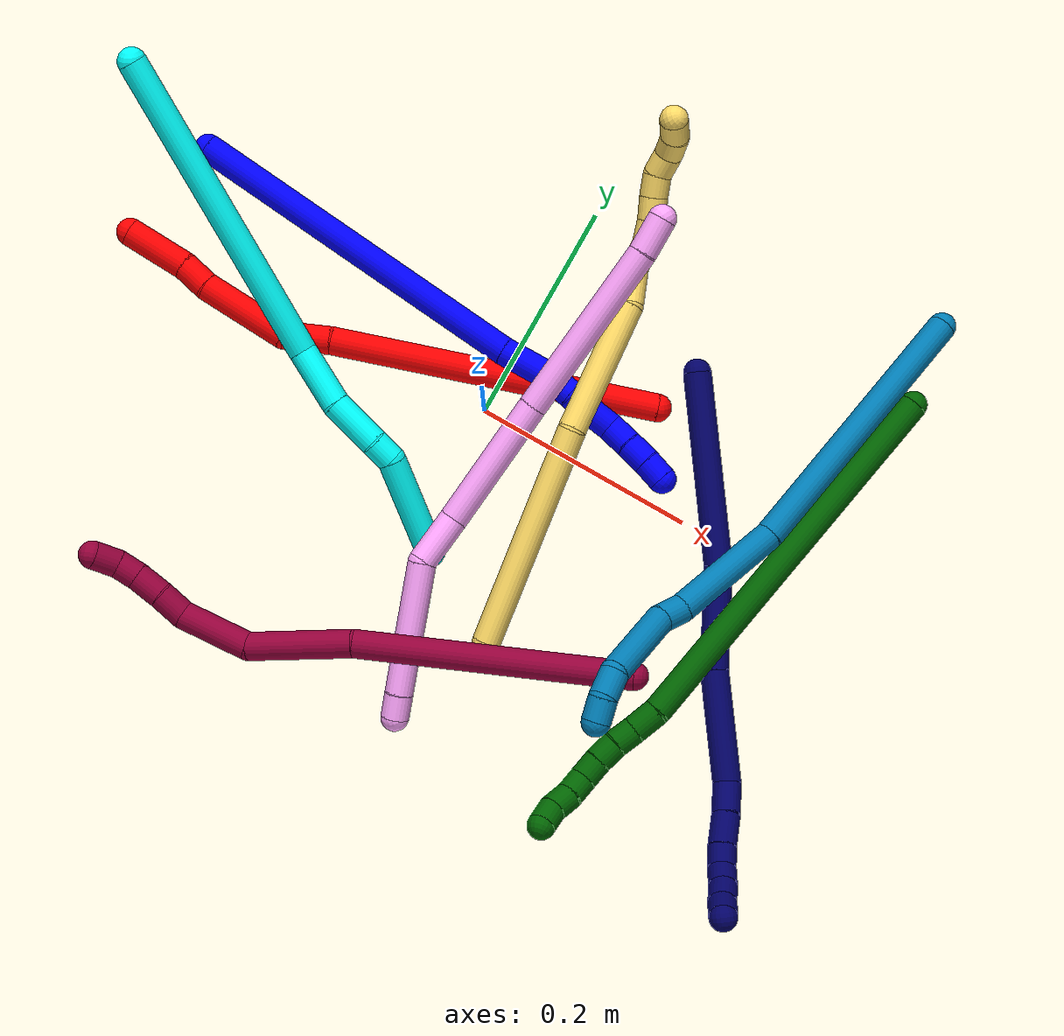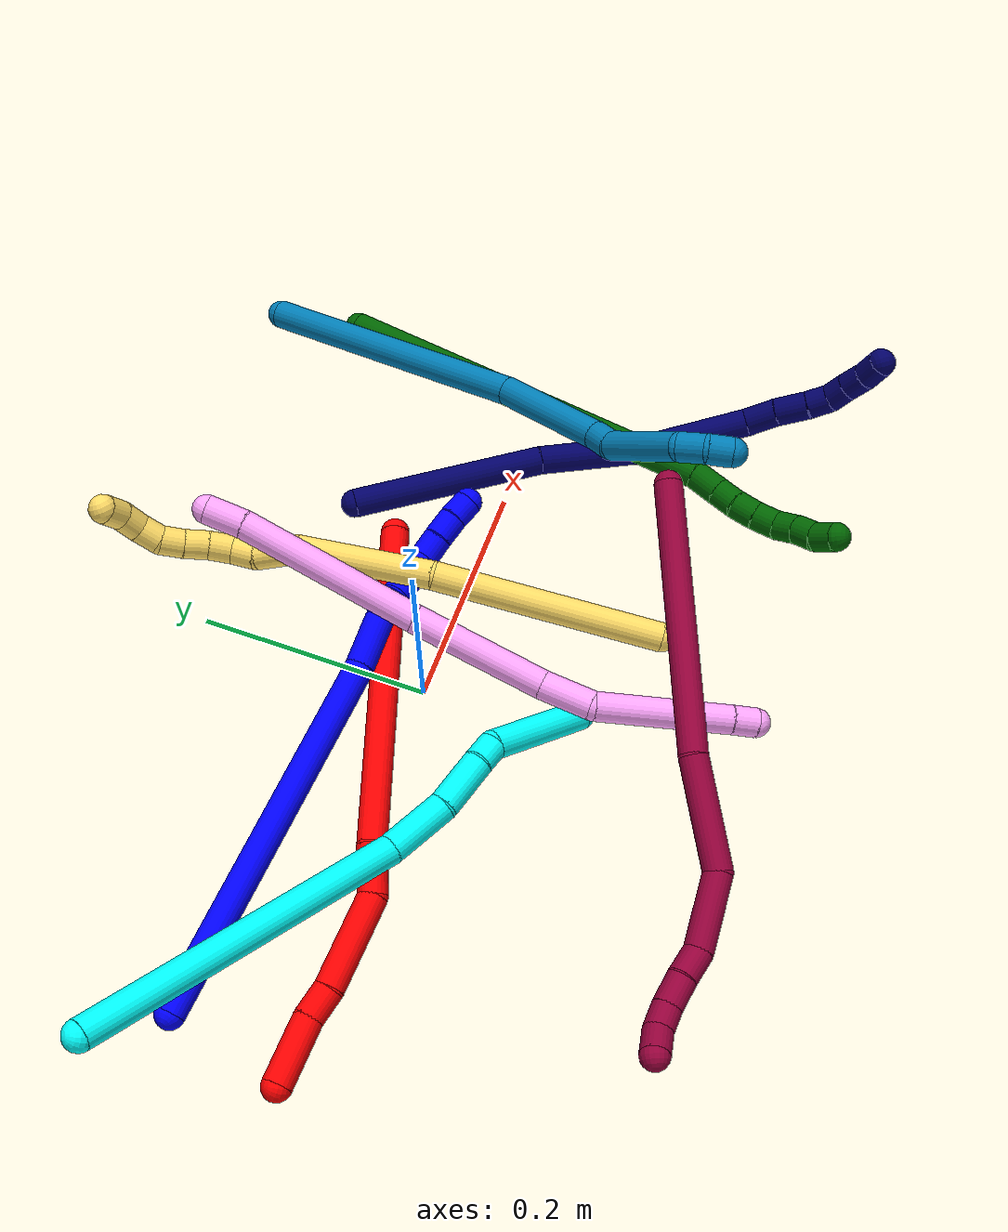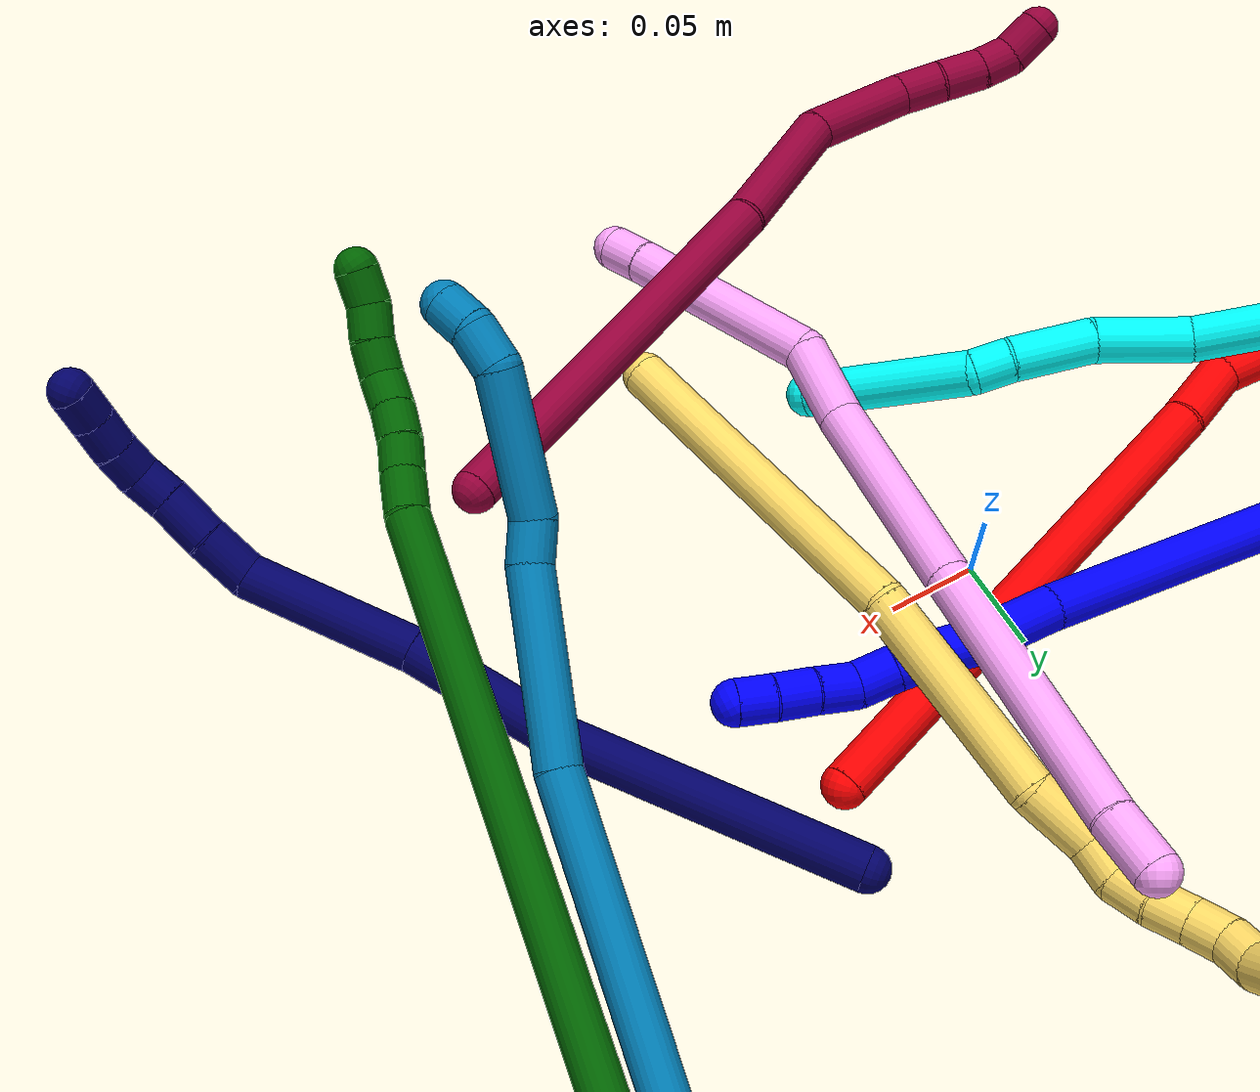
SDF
<sdf version="1.7">
 <world name="default">
  <plugin name="TubeGeneratorPlugin" filename="libtube_generator_plugin.so"/>
  <model name="photoneo_s_sensor">
   <static>1</static>
   <pose>0 0 2 1.57079 1.57079 3.14159</pose>
   <link name="link">
    <inertial><mass>0.1</mass></inertial>
    <sensor name="sensor" type="depth">
     <update_rate>30</update_rate>
     <camera>
      <horizontal_fov>1.22</horizontal_fov>
      <image><width>1920</width><height>1200</height><format>B8G8R8</format></image>
      <clip><near>0.1</near><far>4</far></clip>
      <depth_camera><output>points</output></depth_camera>
     </camera>
     <plugin name="camera_plugin" filename="libgazebo_ros_depth_camera.so">
      <baseline>0.2</baseline>
      <alwaysOn>1</alwaysOn>
      <updateRate>0.0</updateRate>
      <cameraName>camera_ir</cameraName>
      <imageTopicName>/camera/color/image_raw</imageTopicName>
      <cameraInfoTopicName>/camera/color/camera_info</cameraInfoTopicName>
      <depthImageTopicName>/camera/depth/image_raw</depthImageTopicName>
      <depthImageCameraInfoTopicName>/camera/depth/camera_info</depthImageCameraInfoTopicName>
      <pointCloudTopicName>/camera/depth/points</pointCloudTopicName>
      <frameName>fr_optical</frameName>
      <pointCloudCutoff>0.1</pointCloudCutoff>
      <pointCloudCutoffMax>2.0</pointCloudCutoffMax>
      <distortionK1>0</distortionK1>
      <distortionK2>0</distortionK2>
      <distortionK3>0</distortionK3>
      <distortionT1>0</distortionT1>
      <distortionT2>0</distortionT2>
      <CxPrime>0</CxPrime>
      <Cx>0</Cx>
      <Cy>0</Cy>
      <focalLength>0</focalLength>
      <hackBaseline>0</hackBaseline>
     </plugin>
    </sensor>
   </link>
  </model>
  <gravity>0 0 -9.8</gravity>
  <magnetic_field>6e-06 2.3e-05 -4.2e-05</magnetic_field>
  <atmosphere type="adiabatic"/>
  <physics name="default_physics" default="0" type="ode">
   <max_step_size>0.003</max_step_size>
   <real_time_factor>1</real_time_factor>
   <real_time_update_rate>1000</real_time_update_rate>
   <max_contacts>10000</max_contacts>
   <ode>
    <solver>
     <type>quick</type>
     <iters>100</iters>
     <sor>1.3</sor>
     <use_dynamic_moi_rescaling>0</use_dynamic_moi_rescaling>
    </solver>
    <constraints>
     <contact_max_correcting_vel>0</contact_max_correcting_vel>
     <contact_surface_layer>0.001</contact_surface_layer>
     <cfm>0</cfm>
     <erp>0.2</erp>
    </constraints>
   </ode>
  </physics>
  <scene><ambient>0.4 0.4 0.4 1</ambient><background>0.7 0.7 0.7 1</background><shadows>0</shadows></scene>
  <audio><device>default</device></audio>
  <spherical_coordinates>
   <surface_model>EARTH_WGS84</surface_model>
   <latitude_deg>0</latitude_deg>
   <longitude_deg>0</longitude_deg>
   <elevation>0</elevation>
   <heading_deg>0</heading_deg>
  </spherical_coordinates>
  <model name="bin">
   <static>1</static>
   <link name="bottom">
    <collision name="collision-bottom">
     <pose>0 0 -0.01 0 -0 0</pose>
     <geometry><box><size>0.8 0.6 0.02</size></box></geometry>
     <surface>
      <friction><ode><mu>100</mu><mu2>100</mu2></ode></friction>
      <contact><collide_bitmask>65535</collide_bitmask></contact>
     </surface>
    </collision>
   </link>
   <link name="west_wall">
    <collision name="collision-west_wall">
     <pose>-0.41 0 0.1 0 -0 0</pose>
     <geometry><box><size>0.02 0.6 0.2</size></box></geometry>
     <surface>
      <friction><ode><mu>100</mu><mu2>100</mu2></ode></friction>
      <contact><collide_bitmask>65535</collide_bitmask></contact>
     </surface>
    </collision>
   </link>
   <link name="east_wall">
    <collision name="collision-east_wall">
     <pose>0.41 0 0.1 0 -0 0</pose>
     <geometry><box><size>0.02 0.6 0.2</size></box></geometry>
     <surface>
      <friction><ode><mu>100</mu><mu2>100</mu2></ode></friction>
      <contact><collide_bitmask>65535</collide_bitmask></contact>
     </surface>
    </collision>
   </link>
   <link name="south_wall">
    <collision name="collision-south_wall">
     <pose>0 -0.31 0.1 0 -0 0</pose>
     <geometry><box><size>0.8 0.02 0.2</size></box></geometry>
     <surface>
      <friction><ode><mu>100</mu><mu2>100</mu2></ode></friction>
      <contact><collide_bitmask>65535</collide_bitmask></contact>
     </surface>
    </collision>
   </link>
   <link name="north_wall">
    <collision name="collision-north_wall">
     <pose>0 0.31 0.1 0 -0 0</pose>
     <geometry><box><size>0.8 0.02 0.2</size></box></geometry>
     <surface>
      <friction><ode><mu>100</mu><mu2>100</mu2></ode></friction>
      <contact><collide_bitmask>65535</collide_bitmask></contact>
     </surface>
    </collision>
   </link>
  </model>
  <model name="1">
   <static>0</static>
   <link name="1">
    <collision name="collision-cylinder-e_1_1_4">
     <pose>0.062285 -0.010909 -0.146924 3.06748 0.399975 2.77979</pose>
     <geometry><cylinder><radius>0.0125</radius><length>0.319907</length></cylinder></geometry>
     <surface>
      <friction><ode><mu>1.16</mu><mu2>1.16</mu2><slip1>0</slip1><slip2>0</slip2></ode></friction>
      <contact><ode><kp>1e+06</kp><kd>1</kd><max_vel>0</max_vel><min_depth>0.001</min_depth></ode></contact>
     </surface>
    </collision>
    <visual name="visual-cylinder-e_1_1_4">
     <pose>0.062285 -0.010909 -0.146924 3.06748 0.399975 2.77979</pose>
     <geometry><cylinder><radius>0.0125</radius><length>0.319907</length></cylinder></geometry>
     <material><ambient>0 0 1 1</ambient></material>
    </visual>
    <collision name="collision-cylinder-e_2_4_5">
     <pose>0.134944 -0.021646 -0.313919 -3.13303 0.47704 -3.10639</pose>
     <geometry><cylinder><radius>0.0125</radius><length>0.045189</length></cylinder></geometry>
     <surface>
      <friction><ode><mu>1.16</mu><mu2>1.16</mu2><slip1>0</slip1><slip2>0</slip2></ode></friction>
      <contact><ode><kp>1e+06</kp><kd>1</kd><max_vel>0</max_vel><min_depth>0.001</min_depth></ode></contact>
     </surface>
    </collision>
    <visual name="visual-cylinder-e_2_4_5">
     <pose>0.134944 -0.021646 -0.313919 -3.13303 0.47704 -3.10639</pose>
     <geometry><cylinder><radius>0.0125</radius><length>0.045189</length></cylinder></geometry>
     <material><ambient>0 0 1 1</ambient></material>
    </visual>
    <collision name="collision-cylinder-e_3_5_6">
     <pose>0.149942 -0.023481 -0.345628 2.97086 0.373159 2.29038</pose>
     <geometry><cylinder><radius>0.0125</radius><length>0.025365</length></cylinder></geometry>
     <surface>
      <friction><ode><mu>1.16</mu><mu2>1.16</mu2><slip1>0</slip1><slip2>0</slip2></ode></friction>
      <contact><ode><kp>1e+06</kp><kd>1</kd><max_vel>0</max_vel><min_depth>0.001</min_depth></ode></contact>
     </surface>
    </collision>
    <visual name="visual-cylinder-e_3_5_6">
     <pose>0.149942 -0.023481 -0.345628 2.97086 0.373159 2.29038</pose>
     <geometry><cylinder><radius>0.0125</radius><length>0.025365</length></cylinder></geometry>
     <material><ambient>0 0 1 1</ambient></material>
    </visual>
    <collision name="collision-cylinder-e_4_6_7">
     <pose>0.15655 -0.02681 -0.36807 3.01975 0.180286 1.95431</pose>
     <geometry><cylinder><radius>0.0125</radius><length>0.022128</length></cylinder></geometry>
     <surface>
      <friction><ode><mu>1.16</mu><mu2>1.16</mu2><slip1>0</slip1><slip2>0</slip2></ode></friction>
      <contact><ode><kp>1e+06</kp><kd>1</kd><max_vel>0</max_vel><min_depth>0.001</min_depth></ode></contact>
     </surface>
    </collision>
    <visual name="visual-cylinder-e_4_6_7">
     <pose>0.15655 -0.02681 -0.36807 3.01975 0.180286 1.95431</pose>
     <geometry><cylinder><radius>0.0125</radius><length>0.022128</length></cylinder></geometry>
     <material><ambient>0 0 1 1</ambient></material>
    </visual>
    <collision name="collision-cylinder-e_5_7_8">
     <pose>0.160411 -0.02882 -0.389762 3.07857 0.170459 2.43473</pose>
     <geometry><cylinder><radius>0.0125</radius><length>0.02214</length></cylinder></geometry>
     <surface>
      <friction><ode><mu>1.16</mu><mu2>1.16</mu2><slip1>0</slip1><slip2>0</slip2></ode></friction>
      <contact><ode><kp>1e+06</kp><kd>1</kd><max_vel>0</max_vel><min_depth>0.001</min_depth></ode></contact>
     </surface>
    </collision>
    <visual name="visual-cylinder-e_5_7_8">
     <pose>0.160411 -0.02882 -0.389762 3.07857 0.170459 2.43473</pose>
     <geometry><cylinder><radius>0.0125</radius><length>0.02214</length></cylinder></geometry>
     <material><ambient>0 0 1 1</ambient></material>
    </visual>
    <collision name="collision-cylinder-e_6_8_9">
     <pose>0.168013 -0.032539 -0.410363 2.83908 0.512386 2.08763</pose>
     <geometry><cylinder><radius>0.0125</radius><length>0.02335</length></cylinder></geometry>
     <surface>
      <friction><ode><mu>1.16</mu><mu2>1.16</mu2><slip1>0</slip1><slip2>0</slip2></ode></friction>
      <contact><ode><kp>1e+06</kp><kd>1</kd><max_vel>0</max_vel><min_depth>0.001</min_depth></ode></contact>
     </surface>
    </collision>
    <visual name="visual-cylinder-e_6_8_9">
     <pose>0.168013 -0.032539 -0.410363 2.83908 0.512386 2.08763</pose>
     <geometry><cylinder><radius>0.0125</radius><length>0.02335</length></cylinder></geometry>
     <material><ambient>0 0 1 1</ambient></material>
    </visual>
    <collision name="collision-cylinder-e_7_9_10">
     <pose>0.178253 -0.038318 -0.42961 2.86102 0.427193 1.98739</pose>
     <geometry><cylinder><radius>0.0125</radius><length>0.021801</length></cylinder></geometry>
     <surface>
      <friction><ode><mu>1.16</mu><mu2>1.16</mu2><slip1>0</slip1><slip2>0</slip2></ode></friction>
      <contact><ode><kp>1e+06</kp><kd>1</kd><max_vel>0</max_vel><min_depth>0.001</min_depth></ode></contact>
     </surface>
    </collision>
    <visual name="visual-cylinder-e_7_9_10">
     <pose>0.178253 -0.038318 -0.42961 2.86102 0.427193 1.98739</pose>
     <geometry><cylinder><radius>0.0125</radius><length>0.021801</length></cylinder></geometry>
     <material><ambient>0 0 1 1</ambient></material>
    </visual>
    <collision name="collision-cylinder-e_8_10_2">
     <pose>0.186127 -0.04412 -0.448121 2.81354 0.3403 1.60815</pose>
     <geometry><cylinder><radius>0.0125</radius><length>0.020121</length></cylinder></geometry>
     <surface>
      <friction><ode><mu>1.16</mu><mu2>1.16</mu2><slip1>0</slip1><slip2>0</slip2></ode></friction>
      <contact><ode><kp>1e+06</kp><kd>1</kd><max_vel>0</max_vel><min_depth>0.001</min_depth></ode></contact>
     </surface>
    </collision>
    <visual name="visual-cylinder-e_8_10_2">
     <pose>0.186127 -0.04412 -0.448121 2.81354 0.3403 1.60815</pose>
     <geometry><cylinder><radius>0.0125</radius><length>0.020121</length></cylinder></geometry>
     <material><ambient>0 0 1 1</ambient></material>
    </visual>
    <collision name="collision-sphere-2">
     <pose>0.189485 -0.047176 -0.457098 0 -0 0</pose>
     <geometry><sphere><radius>0.0125</radius></sphere></geometry>
     <surface>
      <friction><ode><mu>1.16</mu><mu2>1.16</mu2><slip1>0</slip1><slip2>0</slip2></ode></friction>
      <contact><ode><kp>1e+06</kp><kd>1</kd><max_vel>0</max_vel><min_depth>0.001</min_depth></ode></contact>
     </surface>
    </collision>
    <visual name="visual-sphere-2">
     <pose>0.189485 -0.047176 -0.457098 0 -0 0</pose>
     <geometry><sphere><radius>0.0125</radius></sphere></geometry>
     <material><ambient>0 0 1 1</ambient></material>
    </visual>
    <collision name="collision-sphere-10">
     <pose>0.182769 -0.041065 -0.439143 0 -0 0</pose>
     <geometry><sphere><radius>0.0125</radius></sphere></geometry>
     <surface>
      <friction><ode><mu>1.16</mu><mu2>1.16</mu2><slip1>0</slip1><slip2>0</slip2></ode></friction>
      <contact><ode><kp>1e+06</kp><kd>1</kd><max_vel>0</max_vel><min_depth>0.001</min_depth></ode></contact>
     </surface>
    </collision>
    <visual name="visual-sphere-10">
     <pose>0.182769 -0.041065 -0.439143 0 -0 0</pose>
     <geometry><sphere><radius>0.0125</radius></sphere></geometry>
     <material><ambient>0 0 1 1</ambient></material>
    </visual>
    <collision name="collision-sphere-9">
     <pose>0.173737 -0.03557 -0.420077 0 -0 0</pose>
     <geometry><sphere><radius>0.0125</radius></sphere></geometry>
     <surface>
      <friction><ode><mu>1.16</mu><mu2>1.16</mu2><slip1>0</slip1><slip2>0</slip2></ode></friction>
      <contact><ode><kp>1e+06</kp><kd>1</kd><max_vel>0</max_vel><min_depth>0.001</min_depth></ode></contact>
     </surface>
    </collision>
    <visual name="visual-sphere-9">
     <pose>0.173737 -0.03557 -0.420077 0 -0 0</pose>
     <geometry><sphere><radius>0.0125</radius></sphere></geometry>
     <material><ambient>0 0 1 1</ambient></material>
    </visual>
    <collision name="collision-sphere-4">
     <pose>0.12457 -0.021818 -0.293848 0 -0 0</pose>
     <geometry><sphere><radius>0.0125</radius></sphere></geometry>
     <surface>
      <friction><ode><mu>1.16</mu><mu2>1.16</mu2><slip1>0</slip1><slip2>0</slip2></ode></friction>
      <contact><ode><kp>1e+06</kp><kd>1</kd><max_vel>0</max_vel><min_depth>0.001</min_depth></ode></contact>
     </surface>
    </collision>
    <visual name="visual-sphere-4">
     <pose>0.12457 -0.021818 -0.293848 0 -0 0</pose>
     <geometry><sphere><radius>0.0125</radius></sphere></geometry>
     <material><ambient>0 0 1 1</ambient></material>
    </visual>
    <collision name="collision-sphere-1">
     <geometry><sphere><radius>0.0125</radius></sphere></geometry>
     <surface>
      <friction><ode><mu>1.16</mu><mu2>1.16</mu2><slip1>0</slip1><slip2>0</slip2></ode></friction>
      <contact><ode><kp>1e+06</kp><kd>1</kd><max_vel>0</max_vel><min_depth>0.001</min_depth></ode></contact>
     </surface>
    </collision>
    <visual name="visual-sphere-1">
     <geometry><sphere><radius>0.0125</radius></sphere></geometry>
     <material><ambient>0 0 1 1</ambient></material>
    </visual>
    <collision name="collision-sphere-8">
     <pose>0.162289 -0.029507 -0.40065 0 -0 0</pose>
     <geometry><sphere><radius>0.0125</radius></sphere></geometry>
     <surface>
      <friction><ode><mu>1.16</mu><mu2>1.16</mu2><slip1>0</slip1><slip2>0</slip2></ode></friction>
      <contact><ode><kp>1e+06</kp><kd>1</kd><max_vel>0</max_vel><min_depth>0.001</min_depth></ode></contact>
     </surface>
    </collision>
    <visual name="visual-sphere-8">
     <pose>0.162289 -0.029507 -0.40065 0 -0 0</pose>
     <geometry><sphere><radius>0.0125</radius></sphere></geometry>
     <material><ambient>0 0 1 1</ambient></material>
    </visual>
    <collision name="collision-sphere-5">
     <pose>0.145319 -0.021474 -0.33399 0 -0 0</pose>
     <geometry><sphere><radius>0.0125</radius></sphere></geometry>
     <surface>
      <friction><ode><mu>1.16</mu><mu2>1.16</mu2><slip1>0</slip1><slip2>0</slip2></ode></friction>
      <contact><ode><kp>1e+06</kp><kd>1</kd><max_vel>0</max_vel><min_depth>0.001</min_depth></ode></contact>
     </surface>
    </collision>
    <visual name="visual-sphere-5">
     <pose>0.145319 -0.021474 -0.33399 0 -0 0</pose>
     <geometry><sphere><radius>0.0125</radius></sphere></geometry>
     <material><ambient>0 0 1 1</ambient></material>
    </visual>
    <collision name="collision-sphere-6">
     <pose>0.154566 -0.025487 -0.357266 0 -0 0</pose>
     <geometry><sphere><radius>0.0125</radius></sphere></geometry>
     <surface>
      <friction><ode><mu>1.16</mu><mu2>1.16</mu2><slip1>0</slip1><slip2>0</slip2></ode></friction>
      <contact><ode><kp>1e+06</kp><kd>1</kd><max_vel>0</max_vel><min_depth>0.001</min_depth></ode></contact>
     </surface>
    </collision>
    <visual name="visual-sphere-6">
     <pose>0.154566 -0.025487 -0.357266 0 -0 0</pose>
     <geometry><sphere><radius>0.0125</radius></sphere></geometry>
     <material><ambient>0 0 1 1</ambient></material>
    </visual>
    <collision name="collision-sphere-7">
     <pose>0.158533 -0.028133 -0.378874 0 -0 0</pose>
     <geometry><sphere><radius>0.0125</radius></sphere></geometry>
     <surface>
      <friction><ode><mu>1.16</mu><mu2>1.16</mu2><slip1>0</slip1><slip2>0</slip2></ode></friction>
      <contact><ode><kp>1e+06</kp><kd>1</kd><max_vel>0</max_vel><min_depth>0.001</min_depth></ode></contact>
     </surface>
    </collision>
    <visual name="visual-sphere-7">
     <pose>0.158533 -0.028133 -0.378874 0 -0 0</pose>
     <geometry><sphere><radius>0.0125</radius></sphere></geometry>
     <material><ambient>0 0 1 1</ambient></material>
    </visual>
    <inertial>
     <pose>0.096793 -0.017556 -0.229386 0 -0 0</pose>
     <mass>0.5</mass>
     <inertia>
      <ixx>-0.001458</ixx>
      <ixy>0</ixy>
      <ixz>0</ixz>
      <iyy>0.003498</iyy>
      <iyz>0</iyz>
      <izz>-0.000922</izz>
     </inertia>
    </inertial>
   </link>
   <pose>-0.327049 0.082118 0.012476 -0.499765 -1.17607 0.42895</pose>
  </model>
  <model name="2">
   <static>0</static>
   <link name="2">
    <collision name="collision-cylinder-e_1_1_4">
     <pose>-0.134537 -0.057209 0.006968 1.4496 -1.16607 -1.05724</pose>
     <geometry><cylinder><radius>0.0125</radius><length>0.292722</length></cylinder></geometry>
     <surface>
      <friction><ode><mu>1.16</mu><mu2>1.16</mu2><slip1>0</slip1><slip2>0</slip2></ode></friction>
      <contact><ode><kp>1e+06</kp><kd>1</kd><max_vel>0</max_vel><min_depth>0.001</min_depth></ode></contact>
     </surface>
    </collision>
    <visual name="visual-cylinder-e_1_1_4">
     <pose>-0.134537 -0.057209 0.006968 1.4496 -1.16607 -1.05724</pose>
     <geometry><cylinder><radius>0.0125</radius><length>0.292722</length></cylinder></geometry>
     <material><ambient>1 0 0 1</ambient></material>
    </visual>
    <collision name="collision-cylinder-e_2_4_5">
     <pose>-0.288937 -0.12131 0.01206 1.83654 -1.22562 -1.48758</pose>
     <geometry><cylinder><radius>0.0125</radius><length>0.042216</length></cylinder></geometry>
     <surface>
      <friction><ode><mu>1.16</mu><mu2>1.16</mu2><slip1>0</slip1><slip2>0</slip2></ode></friction>
      <contact><ode><kp>1e+06</kp><kd>1</kd><max_vel>0</max_vel><min_depth>0.001</min_depth></ode></contact>
     </surface>
    </collision>
    <visual name="visual-cylinder-e_2_4_5">
     <pose>-0.288937 -0.12131 0.01206 1.83654 -1.22562 -1.48758</pose>
     <geometry><cylinder><radius>0.0125</radius><length>0.042216</length></cylinder></geometry>
     <material><ambient>1 0 0 1</ambient></material>
    </visual>
    <collision name="collision-cylinder-e_3_5_6">
     <pose>-0.346643 -0.13461 0.023579 0.446233 -1.19687 -0.306979</pose>
     <geometry><cylinder><radius>0.0125</radius><length>0.081304</length></cylinder></geometry>
     <surface>
      <friction><ode><mu>1.16</mu><mu2>1.16</mu2><slip1>0</slip1><slip2>0</slip2></ode></friction>
      <contact><ode><kp>1e+06</kp><kd>1</kd><max_vel>0</max_vel><min_depth>0.001</min_depth></ode></contact>
     </surface>
    </collision>
    <visual name="visual-cylinder-e_3_5_6">
     <pose>-0.346643 -0.13461 0.023579 0.446233 -1.19687 -0.306979</pose>
     <geometry><cylinder><radius>0.0125</radius><length>0.081304</length></cylinder></geometry>
     <material><ambient>1 0 0 1</ambient></material>
    </visual>
    <collision name="collision-cylinder-e_4_6_7">
     <pose>-0.396622 -0.140959 0.042822 -0.010066 -1.12175 0.006323</pose>
     <geometry><cylinder><radius>0.0125</radius><length>0.026944</length></cylinder></geometry>
     <surface>
      <friction><ode><mu>1.16</mu><mu2>1.16</mu2><slip1>0</slip1><slip2>0</slip2></ode></friction>
      <contact><ode><kp>1e+06</kp><kd>1</kd><max_vel>0</max_vel><min_depth>0.001</min_depth></ode></contact>
     </surface>
    </collision>
    <visual name="visual-cylinder-e_4_6_7">
     <pose>-0.396622 -0.140959 0.042822 -0.010066 -1.12175 0.006323</pose>
     <geometry><cylinder><radius>0.0125</radius><length>0.026944</length></cylinder></geometry>
     <material><ambient>1 0 0 1</ambient></material>
    </visual>
    <collision name="collision-cylinder-e_5_7_2">
     <pose>-0.435147 -0.14582 0.057963 0.486879 -1.19163 -0.333657</pose>
     <geometry><cylinder><radius>0.0125</radius><length>0.056814</length></cylinder></geometry>
     <surface>
      <friction><ode><mu>1.16</mu><mu2>1.16</mu2><slip1>0</slip1><slip2>0</slip2></ode></friction>
      <contact><ode><kp>1e+06</kp><kd>1</kd><max_vel>0</max_vel><min_depth>0.001</min_depth></ode></contact>
     </surface>
    </collision>
    <visual name="visual-cylinder-e_5_7_2">
     <pose>-0.435147 -0.14582 0.057963 0.486879 -1.19163 -0.333657</pose>
     <geometry><cylinder><radius>0.0125</radius><length>0.056814</length></cylinder></geometry>
     <material><ambient>1 0 0 1</ambient></material>
    </visual>
    <collision name="collision-sphere-2">
     <pose>-0.461537 -0.150739 0.067256 0 -0 0</pose>
     <geometry><sphere><radius>0.0125</radius></sphere></geometry>
     <surface>
      <friction><ode><mu>1.16</mu><mu2>1.16</mu2><slip1>0</slip1><slip2>0</slip2></ode></friction>
      <contact><ode><kp>1e+06</kp><kd>1</kd><max_vel>0</max_vel><min_depth>0.001</min_depth></ode></contact>
     </surface>
    </collision>
    <visual name="visual-sphere-2">
     <pose>-0.461537 -0.150739 0.067256 0 -0 0</pose>
     <geometry><sphere><radius>0.0125</radius></sphere></geometry>
     <material><ambient>1 0 0 1</ambient></material>
    </visual>
    <collision name="collision-sphere-7">
     <pose>-0.408758 -0.1409 0.04867 0 -0 0</pose>
     <geometry><sphere><radius>0.0125</radius></sphere></geometry>
     <surface>
      <friction><ode><mu>1.16</mu><mu2>1.16</mu2><slip1>0</slip1><slip2>0</slip2></ode></friction>
      <contact><ode><kp>1e+06</kp><kd>1</kd><max_vel>0</max_vel><min_depth>0.001</min_depth></ode></contact>
     </surface>
    </collision>
    <visual name="visual-sphere-7">
     <pose>-0.408758 -0.1409 0.04867 0 -0 0</pose>
     <geometry><sphere><radius>0.0125</radius></sphere></geometry>
     <material><ambient>1 0 0 1</ambient></material>
    </visual>
    <collision name="collision-sphere-6">
     <pose>-0.384486 -0.141018 0.036974 0 -0 0</pose>
     <geometry><sphere><radius>0.0125</radius></sphere></geometry>
     <surface>
      <friction><ode><mu>1.16</mu><mu2>1.16</mu2><slip1>0</slip1><slip2>0</slip2></ode></friction>
      <contact><ode><kp>1e+06</kp><kd>1</kd><max_vel>0</max_vel><min_depth>0.001</min_depth></ode></contact>
     </surface>
    </collision>
    <visual name="visual-sphere-6">
     <pose>-0.384486 -0.141018 0.036974 0 -0 0</pose>
     <geometry><sphere><radius>0.0125</radius></sphere></geometry>
     <material><ambient>1 0 0 1</ambient></material>
    </visual>
    <collision name="collision-sphere-5">
     <pose>-0.3088 -0.128201 0.010184 0 -0 0</pose>
     <geometry><sphere><radius>0.0125</radius></sphere></geometry>
     <surface>
      <friction><ode><mu>1.16</mu><mu2>1.16</mu2><slip1>0</slip1><slip2>0</slip2></ode></friction>
      <contact><ode><kp>1e+06</kp><kd>1</kd><max_vel>0</max_vel><min_depth>0.001</min_depth></ode></contact>
     </surface>
    </collision>
    <visual name="visual-sphere-5">
     <pose>-0.3088 -0.128201 0.010184 0 -0 0</pose>
     <geometry><sphere><radius>0.0125</radius></sphere></geometry>
     <material><ambient>1 0 0 1</ambient></material>
    </visual>
    <collision name="collision-sphere-1">
     <geometry><sphere><radius>0.0125</radius></sphere></geometry>
     <surface>
      <friction><ode><mu>1.16</mu><mu2>1.16</mu2><slip1>0</slip1><slip2>0</slip2></ode></friction>
      <contact><ode><kp>1e+06</kp><kd>1</kd><max_vel>0</max_vel><min_depth>0.001</min_depth></ode></contact>
     </surface>
    </collision>
    <visual name="visual-sphere-1">
     <geometry><sphere><radius>0.0125</radius></sphere></geometry>
     <material><ambient>1 0 0 1</ambient></material>
    </visual>
    <collision name="collision-sphere-4">
     <pose>-0.269073 -0.114418 0.013936 0 -0 0</pose>
     <geometry><sphere><radius>0.0125</radius></sphere></geometry>
     <surface>
      <friction><ode><mu>1.16</mu><mu2>1.16</mu2><slip1>0</slip1><slip2>0</slip2></ode></friction>
      <contact><ode><kp>1e+06</kp><kd>1</kd><max_vel>0</max_vel><min_depth>0.001</min_depth></ode></contact>
     </surface>
    </collision>
    <visual name="visual-sphere-4">
     <pose>-0.269073 -0.114418 0.013936 0 -0 0</pose>
     <geometry><sphere><radius>0.0125</radius></sphere></geometry>
     <material><ambient>1 0 0 1</ambient></material>
    </visual>
    <inertial>
     <pose>-0.230344 -0.089789 0.017825 0 -0 0</pose>
     <mass>0.5</mass>
     <inertia>
      <ixx>-0.000336</ixx>
      <ixy>0</ixy>
      <ixz>0</ixz>
      <iyy>0.001126</iyy>
      <iyz>0</iyz>
      <izz>0.002843</izz>
     </inertia>
    </inertial>
   </link>
   <pose>0.131443 0.076715 0.011492 -0.969111 -0.338057 0.131258</pose>
  </model>
  <model name="3">
   <static>0</static>
   <link name="3">
    <collision name="collision-cylinder-e_1_1_4">
     <pose>0.065262 -0.022928 -0.123762 2.95841 0.478338 2.4211</pose>
     <geometry><cylinder><radius>0.0125</radius><length>0.283562</length></cylinder></geometry>
     <surface>
      <friction><ode><mu>1.16</mu><mu2>1.16</mu2><slip1>0</slip1><slip2>0</slip2></ode></friction>
      <contact><ode><kp>1e+06</kp><kd>1</kd><max_vel>0</max_vel><min_depth>0.001</min_depth></ode></contact>
     </surface>
    </collision>
    <visual name="visual-cylinder-e_1_1_4">
     <pose>0.065262 -0.022928 -0.123762 2.95841 0.478338 2.4211</pose>
     <geometry><cylinder><radius>0.0125</radius><length>0.283562</length></cylinder></geometry>
     <material><ambient>0.003922 1 0.996078 1</ambient></material>
    </visual>
    <collision name="collision-cylinder-e_2_4_5">
     <pose>0.145873 -0.058226 -0.265996 2.55156 0.604235 1.59606</pose>
     <geometry><cylinder><radius>0.0125</radius><length>0.05403</length></cylinder></geometry>
     <surface>
      <friction><ode><mu>1.16</mu><mu2>1.16</mu2><slip1>0</slip1><slip2>0</slip2></ode></friction>
      <contact><ode><kp>1e+06</kp><kd>1</kd><max_vel>0</max_vel><min_depth>0.001</min_depth></ode></contact>
     </surface>
    </collision>
    <visual name="visual-cylinder-e_2_4_5">
     <pose>0.145873 -0.058226 -0.265996 2.55156 0.604235 1.59606</pose>
     <geometry><cylinder><radius>0.0125</radius><length>0.05403</length></cylinder></geometry>
     <material><ambient>0.003922 1 0.996078 1</ambient></material>
    </visual>
    <collision name="collision-cylinder-e_3_5_6">
     <pose>0.17809 -0.07761 -0.298871 2.68834 0.811223 2.15602</pose>
     <geometry><cylinder><radius>0.0125</radius><length>0.046528</length></cylinder></geometry>
     <surface>
      <friction><ode><mu>1.16</mu><mu2>1.16</mu2><slip1>0</slip1><slip2>0</slip2></ode></friction>
      <contact><ode><kp>1e+06</kp><kd>1</kd><max_vel>0</max_vel><min_depth>0.001</min_depth></ode></contact>
     </surface>
    </collision>
    <visual name="visual-cylinder-e_3_5_6">
     <pose>0.17809 -0.07761 -0.298871 2.68834 0.811223 2.15602</pose>
     <geometry><cylinder><radius>0.0125</radius><length>0.046528</length></cylinder></geometry>
     <material><ambient>0.003922 1 0.996078 1</ambient></material>
    </visual>
    <collision name="collision-cylinder-e_4_6_7">
     <pose>0.202299 -0.086346 -0.320569 2.91001 0.774849 2.58623</pose>
     <geometry><cylinder><radius>0.0125</radius><length>0.020982</length></cylinder></geometry>
     <surface>
      <friction><ode><mu>1.16</mu><mu2>1.16</mu2><slip1>0</slip1><slip2>0</slip2></ode></friction>
      <contact><ode><kp>1e+06</kp><kd>1</kd><max_vel>0</max_vel><min_depth>0.001</min_depth></ode></contact>
     </surface>
    </collision>
    <visual name="visual-cylinder-e_4_6_7">
     <pose>0.202299 -0.086346 -0.320569 2.91001 0.774849 2.58623</pose>
     <geometry><cylinder><radius>0.0125</radius><length>0.020982</length></cylinder></geometry>
     <material><ambient>0.003922 1 0.996078 1</ambient></material>
    </visual>
    <collision name="collision-cylinder-e_5_7_2">
     <pose>0.224766 -0.093867 -0.372463 3.01224 0.324474 2.38801</pose>
     <geometry><cylinder><radius>0.0125</radius><length>0.094899</length></cylinder></geometry>
     <surface>
      <friction><ode><mu>1.16</mu><mu2>1.16</mu2><slip1>0</slip1><slip2>0</slip2></ode></friction>
      <contact><ode><kp>1e+06</kp><kd>1</kd><max_vel>0</max_vel><min_depth>0.001</min_depth></ode></contact>
     </surface>
    </collision>
    <visual name="visual-cylinder-e_5_7_2">
     <pose>0.224766 -0.093867 -0.372463 3.01224 0.324474 2.38801</pose>
     <geometry><cylinder><radius>0.0125</radius><length>0.094899</length></cylinder></geometry>
     <material><ambient>0.003922 1 0.996078 1</ambient></material>
    </visual>
    <collision name="collision-sphere-2">
     <pose>0.239893 -0.099669 -0.41706 0 -0 0</pose>
     <geometry><sphere><radius>0.0125</radius></sphere></geometry>
     <surface>
      <friction><ode><mu>1.16</mu><mu2>1.16</mu2><slip1>0</slip1><slip2>0</slip2></ode></friction>
      <contact><ode><kp>1e+06</kp><kd>1</kd><max_vel>0</max_vel><min_depth>0.001</min_depth></ode></contact>
     </surface>
    </collision>
    <visual name="visual-sphere-2">
     <pose>0.239893 -0.099669 -0.41706 0 -0 0</pose>
     <geometry><sphere><radius>0.0125</radius></sphere></geometry>
     <material><ambient>0.003922 1 0.996078 1</ambient></material>
    </visual>
    <collision name="collision-sphere-7">
     <pose>0.209639 -0.088066 -0.327865 0 -0 0</pose>
     <geometry><sphere><radius>0.0125</radius></sphere></geometry>
     <surface>
      <friction><ode><mu>1.16</mu><mu2>1.16</mu2><slip1>0</slip1><slip2>0</slip2></ode></friction>
      <contact><ode><kp>1e+06</kp><kd>1</kd><max_vel>0</max_vel><min_depth>0.001</min_depth></ode></contact>
     </surface>
    </collision>
    <visual name="visual-sphere-7">
     <pose>0.209639 -0.088066 -0.327865 0 -0 0</pose>
     <geometry><sphere><radius>0.0125</radius></sphere></geometry>
     <material><ambient>0.003922 1 0.996078 1</ambient></material>
    </visual>
    <collision name="collision-sphere-6">
     <pose>0.194959 -0.084625 -0.313273 0 -0 0</pose>
     <geometry><sphere><radius>0.0125</radius></sphere></geometry>
     <surface>
      <friction><ode><mu>1.16</mu><mu2>1.16</mu2><slip1>0</slip1><slip2>0</slip2></ode></friction>
      <contact><ode><kp>1e+06</kp><kd>1</kd><max_vel>0</max_vel><min_depth>0.001</min_depth></ode></contact>
     </surface>
    </collision>
    <visual name="visual-sphere-6">
     <pose>0.194959 -0.084625 -0.313273 0 -0 0</pose>
     <geometry><sphere><radius>0.0125</radius></sphere></geometry>
     <material><ambient>0.003922 1 0.996078 1</ambient></material>
    </visual>
    <collision name="collision-sphere-5">
     <pose>0.161221 -0.070595 -0.284468 0 -0 0</pose>
     <geometry><sphere><radius>0.0125</radius></sphere></geometry>
     <surface>
      <friction><ode><mu>1.16</mu><mu2>1.16</mu2><slip1>0</slip1><slip2>0</slip2></ode></friction>
      <contact><ode><kp>1e+06</kp><kd>1</kd><max_vel>0</max_vel><min_depth>0.001</min_depth></ode></contact>
     </surface>
    </collision>
    <visual name="visual-sphere-5">
     <pose>0.161221 -0.070595 -0.284468 0 -0 0</pose>
     <geometry><sphere><radius>0.0125</radius></sphere></geometry>
     <material><ambient>0.003922 1 0.996078 1</ambient></material>
    </visual>
    <collision name="collision-sphere-1">
     <geometry><sphere><radius>0.0125</radius></sphere></geometry>
     <surface>
      <friction><ode><mu>1.16</mu><mu2>1.16</mu2><slip1>0</slip1><slip2>0</slip2></ode></friction>
      <contact><ode><kp>1e+06</kp><kd>1</kd><max_vel>0</max_vel><min_depth>0.001</min_depth></ode></contact>
     </surface>
    </collision>
    <visual name="visual-sphere-1">
     <geometry><sphere><radius>0.0125</radius></sphere></geometry>
     <material><ambient>0.003922 1 0.996078 1</ambient></material>
    </visual>
    <collision name="collision-sphere-4">
     <pose>0.130525 -0.045857 -0.247523 0 -0 0</pose>
     <geometry><sphere><radius>0.0125</radius></sphere></geometry>
     <surface>
      <friction><ode><mu>1.16</mu><mu2>1.16</mu2><slip1>0</slip1><slip2>0</slip2></ode></friction>
      <contact><ode><kp>1e+06</kp><kd>1</kd><max_vel>0</max_vel><min_depth>0.001</min_depth></ode></contact>
     </surface>
    </collision>
    <visual name="visual-sphere-4">
     <pose>0.130525 -0.045857 -0.247523 0 -0 0</pose>
     <geometry><sphere><radius>0.0125</radius></sphere></geometry>
     <material><ambient>0.003922 1 0.996078 1</ambient></material>
    </visual>
    <inertial>
     <pose>0.120496 -0.047956 -0.210888 0 -0 0</pose>
     <mass>0.5</mass>
     <inertia>
      <ixx>-0.000126</ixx>
      <ixy>0</ixy>
      <ixz>0</ixz>
      <iyy>0.002768</iyy>
      <iyz>0</iyz>
      <izz>-0.000625</izz>
     </inertia>
    </inertial>
   </link>
   <pose>-0.388502 0.095954 0.157842 -0.900102 -0.138251 0.468211</pose>
  </model>
  <model name="4">
   <static>0</static>
   <link name="4">
    <collision name="collision-cylinder-e_1_1_4">
     <pose>-0.002465 -0.010578 0.012646 0.696621 -0.148427 -0.053982</pose>
     <geometry><cylinder><radius>0.0125</radius><length>0.03334</length></cylinder></geometry>
     <surface>
      <friction><ode><mu>1.16</mu><mu2>1.16</mu2><slip1>0</slip1><slip2>0</slip2></ode></friction>
      <contact><ode><kp>1e+06</kp><kd>1</kd><max_vel>0</max_vel><min_depth>0.001</min_depth></ode></contact>
     </surface>
    </collision>
    <visual name="visual-cylinder-e_1_1_4">
     <pose>-0.002465 -0.010578 0.012646 0.696621 -0.148427 -0.053982</pose>
     <geometry><cylinder><radius>0.0125</radius><length>0.03334</length></cylinder></geometry>
     <material><ambient>1 0.65098 0.996078 1</ambient></material>
    </visual>
    <collision name="collision-cylinder-e_2_4_5">
     <pose>-0.025425 -0.068291 0.087695 0.646895 -0.256299 -0.086336</pose>
     <geometry><cylinder><radius>0.0125</radius><length>0.161689</length></cylinder></geometry>
     <surface>
      <friction><ode><mu>1.16</mu><mu2>1.16</mu2><slip1>0</slip1><slip2>0</slip2></ode></friction>
      <contact><ode><kp>1e+06</kp><kd>1</kd><max_vel>0</max_vel><min_depth>0.001</min_depth></ode></contact>
     </surface>
    </collision>
    <visual name="visual-cylinder-e_2_4_5">
     <pose>-0.025425 -0.068291 0.087695 0.646895 -0.256299 -0.086336</pose>
     <geometry><cylinder><radius>0.0125</radius><length>0.161689</length></cylinder></geometry>
     <material><ambient>1 0.65098 0.996078 1</ambient></material>
    </visual>
    <collision name="collision-cylinder-e_3_5_6">
     <pose>-0.05855 -0.149653 0.197438 0.626004 -0.212941 -0.069151</pose>
     <geometry><cylinder><radius>0.0125</radius><length>0.119535</length></cylinder></geometry>
     <surface>
      <friction><ode><mu>1.16</mu><mu2>1.16</mu2><slip1>0</slip1><slip2>0</slip2></ode></friction>
      <contact><ode><kp>1e+06</kp><kd>1</kd><max_vel>0</max_vel><min_depth>0.001</min_depth></ode></contact>
     </surface>
    </collision>
    <visual name="visual-cylinder-e_3_5_6">
     <pose>-0.05855 -0.149653 0.197438 0.626004 -0.212941 -0.069151</pose>
     <geometry><cylinder><radius>0.0125</radius><length>0.119535</length></cylinder></geometry>
     <material><ambient>1 0.65098 0.996078 1</ambient></material>
    </visual>
    <collision name="collision-cylinder-e_4_6_7">
     <pose>-0.072377 -0.194679 0.264979 0.490899 -0.05215 -0.013066</pose>
     <geometry><cylinder><radius>0.0125</radius><length>0.045874</length></cylinder></geometry>
     <surface>
      <friction><ode><mu>1.16</mu><mu2>1.16</mu2><slip1>0</slip1><slip2>0</slip2></ode></friction>
      <contact><ode><kp>1e+06</kp><kd>1</kd><max_vel>0</max_vel><min_depth>0.001</min_depth></ode></contact>
     </surface>
    </collision>
    <visual name="visual-cylinder-e_4_6_7">
     <pose>-0.072377 -0.194679 0.264979 0.490899 -0.05215 -0.013066</pose>
     <geometry><cylinder><radius>0.0125</radius><length>0.045874</length></cylinder></geometry>
     <material><ambient>1 0.65098 0.996078 1</ambient></material>
    </visual>
    <collision name="collision-cylinder-e_5_7_8">
     <pose>-0.072443 -0.254835 0.31724 0.994742 0.01918 0.010413</pose>
     <geometry><cylinder><radius>0.0125</radius><length>0.117735</length></cylinder></geometry>
     <surface>
      <friction><ode><mu>1.16</mu><mu2>1.16</mu2><slip1>0</slip1><slip2>0</slip2></ode></friction>
      <contact><ode><kp>1e+06</kp><kd>1</kd><max_vel>0</max_vel><min_depth>0.001</min_depth></ode></contact>
     </surface>
    </collision>
    <visual name="visual-cylinder-e_5_7_8">
     <pose>-0.072443 -0.254835 0.31724 0.994742 0.01918 0.010413</pose>
     <geometry><cylinder><radius>0.0125</radius><length>0.117735</length></cylinder></geometry>
     <material><ambient>1 0.65098 0.996078 1</ambient></material>
    </visual>
    <collision name="collision-cylinder-e_6_8_2">
     <pose>-0.071589 -0.313539 0.35493 1.02868 -0.025227 -0.014255</pose>
     <geometry><cylinder><radius>0.0125</radius><length>0.021827</length></cylinder></geometry>
     <surface>
      <friction><ode><mu>1.16</mu><mu2>1.16</mu2><slip1>0</slip1><slip2>0</slip2></ode></friction>
      <contact><ode><kp>1e+06</kp><kd>1</kd><max_vel>0</max_vel><min_depth>0.001</min_depth></ode></contact>
     </surface>
    </collision>
    <visual name="visual-cylinder-e_6_8_2">
     <pose>-0.071589 -0.313539 0.35493 1.02868 -0.025227 -0.014255</pose>
     <geometry><cylinder><radius>0.0125</radius><length>0.021827</length></cylinder></geometry>
     <material><ambient>1 0.65098 0.996078 1</ambient></material>
    </visual>
    <collision name="collision-sphere-2">
     <pose>-0.071865 -0.322885 0.360559 0 -0 0</pose>
     <geometry><sphere><radius>0.0125</radius></sphere></geometry>
     <surface>
      <friction><ode><mu>1.16</mu><mu2>1.16</mu2><slip1>0</slip1><slip2>0</slip2></ode></friction>
      <contact><ode><kp>1e+06</kp><kd>1</kd><max_vel>0</max_vel><min_depth>0.001</min_depth></ode></contact>
     </surface>
    </collision>
    <visual name="visual-sphere-2">
     <pose>-0.071865 -0.322885 0.360559 0 -0 0</pose>
     <geometry><sphere><radius>0.0125</radius></sphere></geometry>
     <material><ambient>1 0.65098 0.996078 1</ambient></material>
    </visual>
    <collision name="collision-sphere-4">
     <pose>-0.00493 -0.021157 0.025291 0 -0 0</pose>
     <geometry><sphere><radius>0.0125</radius></sphere></geometry>
     <surface>
      <friction><ode><mu>1.16</mu><mu2>1.16</mu2><slip1>0</slip1><slip2>0</slip2></ode></friction>
      <contact><ode><kp>1e+06</kp><kd>1</kd><max_vel>0</max_vel><min_depth>0.001</min_depth></ode></contact>
     </surface>
    </collision>
    <visual name="visual-sphere-4">
     <pose>-0.00493 -0.021157 0.025291 0 -0 0</pose>
     <geometry><sphere><radius>0.0125</radius></sphere></geometry>
     <material><ambient>1 0.65098 0.996078 1</ambient></material>
    </visual>
    <collision name="collision-sphere-1">
     <geometry><sphere><radius>0.0125</radius></sphere></geometry>
     <surface>
      <friction><ode><mu>1.16</mu><mu2>1.16</mu2><slip1>0</slip1><slip2>0</slip2></ode></friction>
      <contact><ode><kp>1e+06</kp><kd>1</kd><max_vel>0</max_vel><min_depth>0.001</min_depth></ode></contact>
     </surface>
    </collision>
    <visual name="visual-sphere-1">
     <geometry><sphere><radius>0.0125</radius></sphere></geometry>
     <material><ambient>1 0.65098 0.996078 1</ambient></material>
    </visual>
    <collision name="collision-sphere-8">
     <pose>-0.071314 -0.304194 0.349301 0 -0 0</pose>
     <geometry><sphere><radius>0.0125</radius></sphere></geometry>
     <surface>
      <friction><ode><mu>1.16</mu><mu2>1.16</mu2><slip1>0</slip1><slip2>0</slip2></ode></friction>
      <contact><ode><kp>1e+06</kp><kd>1</kd><max_vel>0</max_vel><min_depth>0.001</min_depth></ode></contact>
     </surface>
    </collision>
    <visual name="visual-sphere-8">
     <pose>-0.071314 -0.304194 0.349301 0 -0 0</pose>
     <geometry><sphere><radius>0.0125</radius></sphere></geometry>
     <material><ambient>1 0.65098 0.996078 1</ambient></material>
    </visual>
    <collision name="collision-sphere-5">
     <pose>-0.045919 -0.115426 0.150098 0 -0 0</pose>
     <geometry><sphere><radius>0.0125</radius></sphere></geometry>
     <surface>
      <friction><ode><mu>1.16</mu><mu2>1.16</mu2><slip1>0</slip1><slip2>0</slip2></ode></friction>
      <contact><ode><kp>1e+06</kp><kd>1</kd><max_vel>0</max_vel><min_depth>0.001</min_depth></ode></contact>
     </surface>
    </collision>
    <visual name="visual-sphere-5">
     <pose>-0.045919 -0.115426 0.150098 0 -0 0</pose>
     <geometry><sphere><radius>0.0125</radius></sphere></geometry>
     <material><ambient>1 0.65098 0.996078 1</ambient></material>
    </visual>
    <collision name="collision-sphere-6">
     <pose>-0.071181 -0.183881 0.244778 0 -0 0</pose>
     <geometry><sphere><radius>0.0125</radius></sphere></geometry>
     <surface>
      <friction><ode><mu>1.16</mu><mu2>1.16</mu2><slip1>0</slip1><slip2>0</slip2></ode></friction>
      <contact><ode><kp>1e+06</kp><kd>1</kd><max_vel>0</max_vel><min_depth>0.001</min_depth></ode></contact>
     </surface>
    </collision>
    <visual name="visual-sphere-6">
     <pose>-0.071181 -0.183881 0.244778 0 -0 0</pose>
     <geometry><sphere><radius>0.0125</radius></sphere></geometry>
     <material><ambient>1 0.65098 0.996078 1</ambient></material>
    </visual>
    <collision name="collision-sphere-7">
     <pose>-0.073572 -0.205477 0.28518 0 -0 0</pose>
     <geometry><sphere><radius>0.0125</radius></sphere></geometry>
     <surface>
      <friction><ode><mu>1.16</mu><mu2>1.16</mu2><slip1>0</slip1><slip2>0</slip2></ode></friction>
      <contact><ode><kp>1e+06</kp><kd>1</kd><max_vel>0</max_vel><min_depth>0.001</min_depth></ode></contact>
     </surface>
    </collision>
    <visual name="visual-sphere-7">
     <pose>-0.073572 -0.205477 0.28518 0 -0 0</pose>
     <geometry><sphere><radius>0.0125</radius></sphere></geometry>
     <material><ambient>1 0.65098 0.996078 1</ambient></material>
    </visual>
    <inertial>
     <pose>-0.049207 -0.150121 0.190909 0 -0 0</pose>
     <mass>0.5</mass>
     <inertia>
      <ixx>0.000601</ixx>
      <ixy>0</ixy>
      <ixz>0</ixz>
      <iyy>0.000435</iyy>
      <iyz>0</iyz>
      <izz>0.000569</izz>
     </inertia>
    </inertial>
   </link>
   <pose>0.055751 0.20995 0.093913 0.926916 -0.907815 0.042506</pose>
  </model>
  <model name="5">
   <static>0</static>
   <link name="5">
    <collision name="collision-cylinder-e_1_1_4">
     <pose>-0.065914 0.048398 0.055504 -0.717112 -0.730077 0.284503</pose>
     <geometry><cylinder><radius>0.0125</radius><length>0.197664</length></cylinder></geometry>
     <surface>
      <friction><ode><mu>1.16</mu><mu2>1.16</mu2><slip1>0</slip1><slip2>0</slip2></ode></friction>
      <contact><ode><kp>1e+06</kp><kd>1</kd><max_vel>0</max_vel><min_depth>0.001</min_depth></ode></contact>
     </surface>
    </collision>
    <visual name="visual-cylinder-e_1_1_4">
     <pose>-0.065914 0.048398 0.055504 -0.717112 -0.730077 0.284503</pose>
     <geometry><cylinder><radius>0.0125</radius><length>0.197664</length></cylinder></geometry>
     <material><ambient>1 0.858824 0.4 1</ambient></material>
    </visual>
    <collision name="collision-cylinder-e_2_4_5">
     <pose>-0.168321 0.137454 0.135844 -1.02245 -0.653651 0.375831</pose>
     <geometry><cylinder><radius>0.0125</radius><length>0.120027</length></cylinder></geometry>
     <surface>
      <friction><ode><mu>1.16</mu><mu2>1.16</mu2><slip1>0</slip1><slip2>0</slip2></ode></friction>
      <contact><ode><kp>1e+06</kp><kd>1</kd><max_vel>0</max_vel><min_depth>0.001</min_depth></ode></contact>
     </surface>
    </collision>
    <visual name="visual-cylinder-e_2_4_5">
     <pose>-0.168321 0.137454 0.135844 -1.02245 -0.653651 0.375831</pose>
     <geometry><cylinder><radius>0.0125</radius><length>0.120027</length></cylinder></geometry>
     <material><ambient>1 0.858824 0.4 1</ambient></material>
    </visual>
    <collision name="collision-cylinder-e_3_5_6">
     <pose>-0.219019 0.19015 0.163112 -1.37132 -0.857906 0.716043</pose>
     <geometry><cylinder><radius>0.0125</radius><length>0.037555</length></cylinder></geometry>
     <surface>
      <friction><ode><mu>1.16</mu><mu2>1.16</mu2><slip1>0</slip1><slip2>0</slip2></ode></friction>
      <contact><ode><kp>1e+06</kp><kd>1</kd><max_vel>0</max_vel><min_depth>0.001</min_depth></ode></contact>
     </surface>
    </collision>
    <visual name="visual-cylinder-e_3_5_6">
     <pose>-0.219019 0.19015 0.163112 -1.37132 -0.857906 0.716043</pose>
     <geometry><cylinder><radius>0.0125</radius><length>0.037555</length></cylinder></geometry>
     <material><ambient>1 0.858824 0.4 1</ambient></material>
    </visual>
    <collision name="collision-cylinder-e_4_6_7">
     <pose>-0.239356 0.209674 0.170389 -0.996613 -0.602485 0.334938</pose>
     <geometry><cylinder><radius>0.0125</radius><length>0.021644</length></cylinder></geometry>
     <surface>
      <friction><ode><mu>1.16</mu><mu2>1.16</mu2><slip1>0</slip1><slip2>0</slip2></ode></friction>
      <contact><ode><kp>1e+06</kp><kd>1</kd><max_vel>0</max_vel><min_depth>0.001</min_depth></ode></contact>
     </surface>
    </collision>
    <visual name="visual-cylinder-e_4_6_7">
     <pose>-0.239356 0.209674 0.170389 -0.996613 -0.602485 0.334938</pose>
     <geometry><cylinder><radius>0.0125</radius><length>0.021644</length></cylinder></geometry>
     <material><ambient>1 0.858824 0.4 1</ambient></material>
    </visual>
    <collision name="collision-cylinder-e_5_7_8">
     <pose>-0.253833 0.220754 0.181034 -0.55449 -0.885177 0.268128</pose>
     <geometry><cylinder><radius>0.0125</radius><length>0.02156</length></cylinder></geometry>
     <surface>
      <friction><ode><mu>1.16</mu><mu2>1.16</mu2><slip1>0</slip1><slip2>0</slip2></ode></friction>
      <contact><ode><kp>1e+06</kp><kd>1</kd><max_vel>0</max_vel><min_depth>0.001</min_depth></ode></contact>
     </surface>
    </collision>
    <visual name="visual-cylinder-e_5_7_8">
     <pose>-0.253833 0.220754 0.181034 -0.55449 -0.885177 0.268128</pose>
     <geometry><cylinder><radius>0.0125</radius><length>0.02156</length></cylinder></geometry>
     <material><ambient>1 0.858824 0.4 1</ambient></material>
    </visual>
    <collision name="collision-cylinder-e_6_8_9">
     <pose>-0.271144 0.22707 0.191662 -0.513706 -1.01733 0.290847</pose>
     <geometry><cylinder><radius>0.0125</radius><length>0.021082</length></cylinder></geometry>
     <surface>
      <friction><ode><mu>1.16</mu><mu2>1.16</mu2><slip1>0</slip1><slip2>0</slip2></ode></friction>
      <contact><ode><kp>1e+06</kp><kd>1</kd><max_vel>0</max_vel><min_depth>0.001</min_depth></ode></contact>
     </surface>
    </collision>
    <visual name="visual-cylinder-e_6_8_9">
     <pose>-0.271144 0.22707 0.191662 -0.513706 -1.01733 0.290847</pose>
     <geometry><cylinder><radius>0.0125</radius><length>0.021082</length></cylinder></geometry>
     <material><ambient>1 0.858824 0.4 1</ambient></material>
    </visual>
    <collision name="collision-cylinder-e_7_9_10">
     <pose>-0.288144 0.232014 0.202093 -0.377368 -0.927008 0.190311</pose>
     <geometry><cylinder><radius>0.0125</radius><length>0.020088</length></cylinder></geometry>
     <surface>
      <friction><ode><mu>1.16</mu><mu2>1.16</mu2><slip1>0</slip1><slip2>0</slip2></ode></friction>
      <contact><ode><kp>1e+06</kp><kd>1</kd><max_vel>0</max_vel><min_depth>0.001</min_depth></ode></contact>
     </surface>
    </collision>
    <visual name="visual-cylinder-e_7_9_10">
     <pose>-0.288144 0.232014 0.202093 -0.377368 -0.927008 0.190311</pose>
     <geometry><cylinder><radius>0.0125</radius><length>0.020088</length></cylinder></geometry>
     <material><ambient>1 0.858824 0.4 1</ambient></material>
    </visual>
    <collision name="collision-cylinder-e_8_10_11">
     <pose>-0.301521 0.236766 0.215836 -0.301351 -0.559971 0.087256</pose>
     <geometry><cylinder><radius>0.0125</radius><length>0.02012</length></cylinder></geometry>
     <surface>
      <friction><ode><mu>1.16</mu><mu2>1.16</mu2><slip1>0</slip1><slip2>0</slip2></ode></friction>
      <contact><ode><kp>1e+06</kp><kd>1</kd><max_vel>0</max_vel><min_depth>0.001</min_depth></ode></contact>
     </surface>
    </collision>
    <visual name="visual-cylinder-e_8_10_11">
     <pose>-0.301521 0.236766 0.215836 -0.301351 -0.559971 0.087256</pose>
     <geometry><cylinder><radius>0.0125</radius><length>0.02012</length></cylinder></geometry>
     <material><ambient>1 0.858824 0.4 1</ambient></material>
    </visual>
    <collision name="collision-cylinder-e_9_11_12">
     <pose>-0.311984 0.237765 0.232515 0.177343 -0.533064 -0.048537</pose>
     <geometry><cylinder><radius>0.0125</radius><length>0.020146</length></cylinder></geometry>
     <surface>
      <friction><ode><mu>1.16</mu><mu2>1.16</mu2><slip1>0</slip1><slip2>0</slip2></ode></friction>
      <contact><ode><kp>1e+06</kp><kd>1</kd><max_vel>0</max_vel><min_depth>0.001</min_depth></ode></contact>
     </surface>
    </collision>
    <visual name="visual-cylinder-e_9_11_12">
     <pose>-0.311984 0.237765 0.232515 0.177343 -0.533064 -0.048537</pose>
     <geometry><cylinder><radius>0.0125</radius><length>0.020146</length></cylinder></geometry>
     <material><ambient>1 0.858824 0.4 1</ambient></material>
    </visual>
    <collision name="collision-cylinder-e_10_12_2">
     <pose>-0.323601 0.232231 0.247604 0.548707 -0.702558 -0.205565</pose>
     <geometry><cylinder><radius>0.0125</radius><length>0.020116</length></cylinder></geometry>
     <surface>
      <friction><ode><mu>1.16</mu><mu2>1.16</mu2><slip1>0</slip1><slip2>0</slip2></ode></friction>
      <contact><ode><kp>1e+06</kp><kd>1</kd><max_vel>0</max_vel><min_depth>0.001</min_depth></ode></contact>
     </surface>
    </collision>
    <visual name="visual-cylinder-e_10_12_2">
     <pose>-0.323601 0.232231 0.247604 0.548707 -0.702558 -0.205565</pose>
     <geometry><cylinder><radius>0.0125</radius><length>0.020116</length></cylinder></geometry>
     <material><ambient>1 0.858824 0.4 1</ambient></material>
    </visual>
    <collision name="collision-sphere-2">
     <pose>-0.330101 0.228227 0.254153 0 -0 0</pose>
     <geometry><sphere><radius>0.0125</radius></sphere></geometry>
     <surface>
      <friction><ode><mu>1.16</mu><mu2>1.16</mu2><slip1>0</slip1><slip2>0</slip2></ode></friction>
      <contact><ode><kp>1e+06</kp><kd>1</kd><max_vel>0</max_vel><min_depth>0.001</min_depth></ode></contact>
     </surface>
    </collision>
    <visual name="visual-sphere-2">
     <pose>-0.330101 0.228227 0.254153 0 -0 0</pose>
     <geometry><sphere><radius>0.0125</radius></sphere></geometry>
     <material><ambient>1 0.858824 0.4 1</ambient></material>
    </visual>
    <collision name="collision-sphere-12">
     <pose>-0.317102 0.236235 0.241054 0 -0 0</pose>
     <geometry><sphere><radius>0.0125</radius></sphere></geometry>
     <surface>
      <friction><ode><mu>1.16</mu><mu2>1.16</mu2><slip1>0</slip1><slip2>0</slip2></ode></friction>
      <contact><ode><kp>1e+06</kp><kd>1</kd><max_vel>0</max_vel><min_depth>0.001</min_depth></ode></contact>
     </surface>
    </collision>
    <visual name="visual-sphere-12">
     <pose>-0.317102 0.236235 0.241054 0 -0 0</pose>
     <geometry><sphere><radius>0.0125</radius></sphere></geometry>
     <material><ambient>1 0.858824 0.4 1</ambient></material>
    </visual>
    <collision name="collision-sphere-11">
     <pose>-0.306865 0.239295 0.223976 0 -0 0</pose>
     <geometry><sphere><radius>0.0125</radius></sphere></geometry>
     <surface>
      <friction><ode><mu>1.16</mu><mu2>1.16</mu2><slip1>0</slip1><slip2>0</slip2></ode></friction>
      <contact><ode><kp>1e+06</kp><kd>1</kd><max_vel>0</max_vel><min_depth>0.001</min_depth></ode></contact>
     </surface>
    </collision>
    <visual name="visual-sphere-11">
     <pose>-0.306865 0.239295 0.223976 0 -0 0</pose>
     <geometry><sphere><radius>0.0125</radius></sphere></geometry>
     <material><ambient>1 0.858824 0.4 1</ambient></material>
    </visual>
    <collision name="collision-sphere-10">
     <pose>-0.296178 0.234236 0.207697 0 -0 0</pose>
     <geometry><sphere><radius>0.0125</radius></sphere></geometry>
     <surface>
      <friction><ode><mu>1.16</mu><mu2>1.16</mu2><slip1>0</slip1><slip2>0</slip2></ode></friction>
      <contact><ode><kp>1e+06</kp><kd>1</kd><max_vel>0</max_vel><min_depth>0.001</min_depth></ode></contact>
     </surface>
    </collision>
    <visual name="visual-sphere-10">
     <pose>-0.296178 0.234236 0.207697 0 -0 0</pose>
     <geometry><sphere><radius>0.0125</radius></sphere></geometry>
     <material><ambient>1 0.858824 0.4 1</ambient></material>
    </visual>
    <collision name="collision-sphere-9">
     <pose>-0.280111 0.229793 0.196488 0 -0 0</pose>
     <geometry><sphere><radius>0.0125</radius></sphere></geometry>
     <surface>
      <friction><ode><mu>1.16</mu><mu2>1.16</mu2><slip1>0</slip1><slip2>0</slip2></ode></friction>
      <contact><ode><kp>1e+06</kp><kd>1</kd><max_vel>0</max_vel><min_depth>0.001</min_depth></ode></contact>
     </surface>
    </collision>
    <visual name="visual-sphere-9">
     <pose>-0.280111 0.229793 0.196488 0 -0 0</pose>
     <geometry><sphere><radius>0.0125</radius></sphere></geometry>
     <material><ambient>1 0.858824 0.4 1</ambient></material>
    </visual>
    <collision name="collision-sphere-4">
     <pose>-0.131827 0.096797 0.111009 0 -0 0</pose>
     <geometry><sphere><radius>0.0125</radius></sphere></geometry>
     <surface>
      <friction><ode><mu>1.16</mu><mu2>1.16</mu2><slip1>0</slip1><slip2>0</slip2></ode></friction>
      <contact><ode><kp>1e+06</kp><kd>1</kd><max_vel>0</max_vel><min_depth>0.001</min_depth></ode></contact>
     </surface>
    </collision>
    <visual name="visual-sphere-4">
     <pose>-0.131827 0.096797 0.111009 0 -0 0</pose>
     <geometry><sphere><radius>0.0125</radius></sphere></geometry>
     <material><ambient>1 0.858824 0.4 1</ambient></material>
    </visual>
    <collision name="collision-sphere-1">
     <geometry><sphere><radius>0.0125</radius></sphere></geometry>
     <surface>
      <friction><ode><mu>1.16</mu><mu2>1.16</mu2><slip1>0</slip1><slip2>0</slip2></ode></friction>
      <contact><ode><kp>1e+06</kp><kd>1</kd><max_vel>0</max_vel><min_depth>0.001</min_depth></ode></contact>
     </surface>
    </collision>
    <visual name="visual-sphere-1">
     <geometry><sphere><radius>0.0125</radius></sphere></geometry>
     <material><ambient>1 0.858824 0.4 1</ambient></material>
    </visual>
    <collision name="collision-sphere-8">
     <pose>-0.262177 0.224347 0.186837 0 -0 0</pose>
     <geometry><sphere><radius>0.0125</radius></sphere></geometry>
     <surface>
      <friction><ode><mu>1.16</mu><mu2>1.16</mu2><slip1>0</slip1><slip2>0</slip2></ode></friction>
      <contact><ode><kp>1e+06</kp><kd>1</kd><max_vel>0</max_vel><min_depth>0.001</min_depth></ode></contact>
     </surface>
    </collision>
    <visual name="visual-sphere-8">
     <pose>-0.262177 0.224347 0.186837 0 -0 0</pose>
     <geometry><sphere><radius>0.0125</radius></sphere></geometry>
     <material><ambient>1 0.858824 0.4 1</ambient></material>
    </visual>
    <collision name="collision-sphere-5">
     <pose>-0.204814 0.178112 0.160678 0 -0 0</pose>
     <geometry><sphere><radius>0.0125</radius></sphere></geometry>
     <surface>
      <friction><ode><mu>1.16</mu><mu2>1.16</mu2><slip1>0</slip1><slip2>0</slip2></ode></friction>
      <contact><ode><kp>1e+06</kp><kd>1</kd><max_vel>0</max_vel><min_depth>0.001</min_depth></ode></contact>
     </surface>
    </collision>
    <visual name="visual-sphere-5">
     <pose>-0.204814 0.178112 0.160678 0 -0 0</pose>
     <geometry><sphere><radius>0.0125</radius></sphere></geometry>
     <material><ambient>1 0.858824 0.4 1</ambient></material>
    </visual>
    <collision name="collision-sphere-6">
     <pose>-0.233223 0.202187 0.165546 0 -0 0</pose>
     <geometry><sphere><radius>0.0125</radius></sphere></geometry>
     <surface>
      <friction><ode><mu>1.16</mu><mu2>1.16</mu2><slip1>0</slip1><slip2>0</slip2></ode></friction>
      <contact><ode><kp>1e+06</kp><kd>1</kd><max_vel>0</max_vel><min_depth>0.001</min_depth></ode></contact>
     </surface>
    </collision>
    <visual name="visual-sphere-6">
     <pose>-0.233223 0.202187 0.165546 0 -0 0</pose>
     <geometry><sphere><radius>0.0125</radius></sphere></geometry>
     <material><ambient>1 0.858824 0.4 1</ambient></material>
    </visual>
    <collision name="collision-sphere-7">
     <pose>-0.245489 0.21716 0.175232 0 -0 0</pose>
     <geometry><sphere><radius>0.0125</radius></sphere></geometry>
     <surface>
      <friction><ode><mu>1.16</mu><mu2>1.16</mu2><slip1>0</slip1><slip2>0</slip2></ode></friction>
      <contact><ode><kp>1e+06</kp><kd>1</kd><max_vel>0</max_vel><min_depth>0.001</min_depth></ode></contact>
     </surface>
    </collision>
    <visual name="visual-sphere-7">
     <pose>-0.245489 0.21716 0.175232 0 -0 0</pose>
     <geometry><sphere><radius>0.0125</radius></sphere></geometry>
     <material><ambient>1 0.858824 0.4 1</ambient></material>
    </visual>
    <inertial>
     <pose>-0.164951 0.132352 0.126201 0 -0 0</pose>
     <mass>0.5</mass>
     <inertia>
      <ixx>0.000743</ixx>
      <ixy>0</ixy>
      <ixz>0</ixz>
      <iyy>0.000866</iyy>
      <iyz>0</iyz>
      <izz>0.000131</izz>
     </inertia>
    </inertial>
   </link>
   <pose>0.102319 -0.17594 0.034385 -0.760514 0.122195 -0.591699</pose>
  </model>
  <model name="6">
   <static>0</static>
   <link name="6">
    <collision name="collision-cylinder-e_1_1_4">
     <pose>0.034638 -0.074885 -0.155819 2.6936 0.197738 0.821285</pose>
     <geometry><cylinder><radius>0.0125</radius><length>0.352631</length></cylinder></geometry>
     <surface>
      <friction><ode><mu>1.16</mu><mu2>1.16</mu2><slip1>0</slip1><slip2>0</slip2></ode></friction>
      <contact><ode><kp>1e+06</kp><kd>1</kd><max_vel>0</max_vel><min_depth>0.001</min_depth></ode></contact>
     </surface>
    </collision>
    <visual name="visual-cylinder-e_1_1_4">
     <pose>0.034638 -0.074885 -0.155819 2.6936 0.197738 0.821285</pose>
     <geometry><cylinder><radius>0.0125</radius><length>0.352631</length></cylinder></geometry>
     <material><ambient>0 0.392157 0.003922 1</ambient></material>
    </visual>
    <collision name="collision-cylinder-e_2_4_5">
     <pose>0.073545 -0.156784 -0.321504 2.52354 0.33909 0.984391</pose>
     <geometry><cylinder><radius>0.0125</radius><length>0.025671</length></cylinder></geometry>
     <surface>
      <friction><ode><mu>1.16</mu><mu2>1.16</mu2><slip1>0</slip1><slip2>0</slip2></ode></friction>
      <contact><ode><kp>1e+06</kp><kd>1</kd><max_vel>0</max_vel><min_depth>0.001</min_depth></ode></contact>
     </surface>
    </collision>
    <visual name="visual-cylinder-e_2_4_5">
     <pose>0.073545 -0.156784 -0.321504 2.52354 0.33909 0.984391</pose>
     <geometry><cylinder><radius>0.0125</radius><length>0.025671</length></cylinder></geometry>
     <material><ambient>0 0.392157 0.003922 1</ambient></material>
    </visual>
    <collision name="collision-cylinder-e_3_5_6">
     <pose>0.081895 -0.168458 -0.339316 2.61123 0.416997 1.32367</pose>
     <geometry><cylinder><radius>0.0125</radius><length>0.020152</length></cylinder></geometry>
     <surface>
      <friction><ode><mu>1.16</mu><mu2>1.16</mu2><slip1>0</slip1><slip2>0</slip2></ode></friction>
      <contact><ode><kp>1e+06</kp><kd>1</kd><max_vel>0</max_vel><min_depth>0.001</min_depth></ode></contact>
     </surface>
    </collision>
    <visual name="visual-cylinder-e_3_5_6">
     <pose>0.081895 -0.168458 -0.339316 2.61123 0.416997 1.32367</pose>
     <geometry><cylinder><radius>0.0125</radius><length>0.020152</length></cylinder></geometry>
     <material><ambient>0 0.392157 0.003922 1</ambient></material>
    </visual>
    <collision name="collision-cylinder-e_4_6_7">
     <pose>0.08877 -0.178004 -0.3558 2.62179 0.276777 0.964957</pose>
     <geometry><cylinder><radius>0.0125</radius><length>0.020451</length></cylinder></geometry>
     <surface>
      <friction><ode><mu>1.16</mu><mu2>1.16</mu2><slip1>0</slip1><slip2>0</slip2></ode></friction>
      <contact><ode><kp>1e+06</kp><kd>1</kd><max_vel>0</max_vel><min_depth>0.001</min_depth></ode></contact>
     </surface>
    </collision>
    <visual name="visual-cylinder-e_4_6_7">
     <pose>0.08877 -0.178004 -0.3558 2.62179 0.276777 0.964957</pose>
     <geometry><cylinder><radius>0.0125</radius><length>0.020451</length></cylinder></geometry>
     <material><ambient>0 0.392157 0.003922 1</ambient></material>
    </visual>
    <collision name="collision-cylinder-e_5_7_8">
     <pose>0.093592 -0.187281 -0.373366 2.68893 0.199292 0.819206</pose>
     <geometry><cylinder><radius>0.0125</radius><length>0.020486</length></cylinder></geometry>
     <surface>
      <friction><ode><mu>1.16</mu><mu2>1.16</mu2><slip1>0</slip1><slip2>0</slip2></ode></friction>
      <contact><ode><kp>1e+06</kp><kd>1</kd><max_vel>0</max_vel><min_depth>0.001</min_depth></ode></contact>
     </surface>
    </collision>
    <visual name="visual-cylinder-e_5_7_8">
     <pose>0.093592 -0.187281 -0.373366 2.68893 0.199292 0.819206</pose>
     <geometry><cylinder><radius>0.0125</radius><length>0.020486</length></cylinder></geometry>
     <material><ambient>0 0.392157 0.003922 1</ambient></material>
    </visual>
    <collision name="collision-cylinder-e_6_8_9">
     <pose>0.098855 -0.192391 -0.391975 3.06663 0.324867 2.69167</pose>
     <geometry><cylinder><radius>0.0125</radius><length>0.020273</length></cylinder></geometry>
     <surface>
      <friction><ode><mu>1.16</mu><mu2>1.16</mu2><slip1>0</slip1><slip2>0</slip2></ode></friction>
      <contact><ode><kp>1e+06</kp><kd>1</kd><max_vel>0</max_vel><min_depth>0.001</min_depth></ode></contact>
     </surface>
    </collision>
    <visual name="visual-cylinder-e_6_8_9">
     <pose>0.098855 -0.192391 -0.391975 3.06663 0.324867 2.69167</pose>
     <geometry><cylinder><radius>0.0125</radius><length>0.020273</length></cylinder></geometry>
     <material><ambient>0 0.392157 0.003922 1</ambient></material>
    </visual>
    <collision name="collision-cylinder-e_7_9_10">
     <pose>0.106909 -0.194246 -0.410365 3.01348 0.496976 2.64634</pose>
     <geometry><cylinder><radius>0.0125</radius><length>0.020213</length></cylinder></geometry>
     <surface>
      <friction><ode><mu>1.16</mu><mu2>1.16</mu2><slip1>0</slip1><slip2>0</slip2></ode></friction>
      <contact><ode><kp>1e+06</kp><kd>1</kd><max_vel>0</max_vel><min_depth>0.001</min_depth></ode></contact>
     </surface>
    </collision>
    <visual name="visual-cylinder-e_7_9_10">
     <pose>0.106909 -0.194246 -0.410365 3.01348 0.496976 2.64634</pose>
     <geometry><cylinder><radius>0.0125</radius><length>0.020213</length></cylinder></geometry>
     <material><ambient>0 0.392157 0.003922 1</ambient></material>
    </visual>
    <collision name="collision-cylinder-e_8_10_2">
     <pose>0.114563 -0.194063 -0.428739 -3.00464 0.285697 -2.25167</pose>
     <geometry><cylinder><radius>0.0125</radius><length>0.020124</length></cylinder></geometry>
     <surface>
      <friction><ode><mu>1.16</mu><mu2>1.16</mu2><slip1>0</slip1><slip2>0</slip2></ode></friction>
      <contact><ode><kp>1e+06</kp><kd>1</kd><max_vel>0</max_vel><min_depth>0.001</min_depth></ode></contact>
     </surface>
    </collision>
    <visual name="visual-cylinder-e_8_10_2">
     <pose>0.114563 -0.194063 -0.428739 -3.00464 0.285697 -2.25167</pose>
     <geometry><cylinder><radius>0.0125</radius><length>0.020124</length></cylinder></geometry>
     <material><ambient>0 0.392157 0.003922 1</ambient></material>
    </visual>
    <collision name="collision-sphere-2">
     <pose>0.117399 -0.192745 -0.438303 0 -0 0</pose>
     <geometry><sphere><radius>0.0125</radius></sphere></geometry>
     <surface>
      <friction><ode><mu>1.16</mu><mu2>1.16</mu2><slip1>0</slip1><slip2>0</slip2></ode></friction>
      <contact><ode><kp>1e+06</kp><kd>1</kd><max_vel>0</max_vel><min_depth>0.001</min_depth></ode></contact>
     </surface>
    </collision>
    <visual name="visual-sphere-2">
     <pose>0.117399 -0.192745 -0.438303 0 -0 0</pose>
     <geometry><sphere><radius>0.0125</radius></sphere></geometry>
     <material><ambient>0 0.392157 0.003922 1</ambient></material>
    </visual>
    <collision name="collision-sphere-10">
     <pose>0.111728 -0.195381 -0.419176 0 -0 0</pose>
     <geometry><sphere><radius>0.0125</radius></sphere></geometry>
     <surface>
      <friction><ode><mu>1.16</mu><mu2>1.16</mu2><slip1>0</slip1><slip2>0</slip2></ode></friction>
      <contact><ode><kp>1e+06</kp><kd>1</kd><max_vel>0</max_vel><min_depth>0.001</min_depth></ode></contact>
     </surface>
    </collision>
    <visual name="visual-sphere-10">
     <pose>0.111728 -0.195381 -0.419176 0 -0 0</pose>
     <geometry><sphere><radius>0.0125</radius></sphere></geometry>
     <material><ambient>0 0.392157 0.003922 1</ambient></material>
    </visual>
    <collision name="collision-sphere-9">
     <pose>0.102091 -0.193111 -0.401554 0 -0 0</pose>
     <geometry><sphere><radius>0.0125</radius></sphere></geometry>
     <surface>
      <friction><ode><mu>1.16</mu><mu2>1.16</mu2><slip1>0</slip1><slip2>0</slip2></ode></friction>
      <contact><ode><kp>1e+06</kp><kd>1</kd><max_vel>0</max_vel><min_depth>0.001</min_depth></ode></contact>
     </surface>
    </collision>
    <visual name="visual-sphere-9">
     <pose>0.102091 -0.193111 -0.401554 0 -0 0</pose>
     <geometry><sphere><radius>0.0125</radius></sphere></geometry>
     <material><ambient>0 0.392157 0.003922 1</ambient></material>
    </visual>
    <collision name="collision-sphere-4">
     <pose>0.069275 -0.149769 -0.311638 0 -0 0</pose>
     <geometry><sphere><radius>0.0125</radius></sphere></geometry>
     <surface>
      <friction><ode><mu>1.16</mu><mu2>1.16</mu2><slip1>0</slip1><slip2>0</slip2></ode></friction>
      <contact><ode><kp>1e+06</kp><kd>1</kd><max_vel>0</max_vel><min_depth>0.001</min_depth></ode></contact>
     </surface>
    </collision>
    <visual name="visual-sphere-4">
     <pose>0.069275 -0.149769 -0.311638 0 -0 0</pose>
     <geometry><sphere><radius>0.0125</radius></sphere></geometry>
     <material><ambient>0 0.392157 0.003922 1</ambient></material>
    </visual>
    <collision name="collision-sphere-1">
     <geometry><sphere><radius>0.0125</radius></sphere></geometry>
     <surface>
      <friction><ode><mu>1.16</mu><mu2>1.16</mu2><slip1>0</slip1><slip2>0</slip2></ode></friction>
      <contact><ode><kp>1e+06</kp><kd>1</kd><max_vel>0</max_vel><min_depth>0.001</min_depth></ode></contact>
     </surface>
    </collision>
    <visual name="visual-sphere-1">
     <geometry><sphere><radius>0.0125</radius></sphere></geometry>
     <material><ambient>0 0.392157 0.003922 1</ambient></material>
    </visual>
    <collision name="collision-sphere-8">
     <pose>0.09562 -0.191672 -0.382395 0 -0 0</pose>
     <geometry><sphere><radius>0.0125</radius></sphere></geometry>
     <surface>
      <friction><ode><mu>1.16</mu><mu2>1.16</mu2><slip1>0</slip1><slip2>0</slip2></ode></friction>
      <contact><ode><kp>1e+06</kp><kd>1</kd><max_vel>0</max_vel><min_depth>0.001</min_depth></ode></contact>
     </surface>
    </collision>
    <visual name="visual-sphere-8">
     <pose>0.09562 -0.191672 -0.382395 0 -0 0</pose>
     <geometry><sphere><radius>0.0125</radius></sphere></geometry>
     <material><ambient>0 0.392157 0.003922 1</ambient></material>
    </visual>
    <collision name="collision-sphere-5">
     <pose>0.077814 -0.163798 -0.331369 0 -0 0</pose>
     <geometry><sphere><radius>0.0125</radius></sphere></geometry>
     <surface>
      <friction><ode><mu>1.16</mu><mu2>1.16</mu2><slip1>0</slip1><slip2>0</slip2></ode></friction>
      <contact><ode><kp>1e+06</kp><kd>1</kd><max_vel>0</max_vel><min_depth>0.001</min_depth></ode></contact>
     </surface>
    </collision>
    <visual name="visual-sphere-5">
     <pose>0.077814 -0.163798 -0.331369 0 -0 0</pose>
     <geometry><sphere><radius>0.0125</radius></sphere></geometry>
     <material><ambient>0 0.392157 0.003922 1</ambient></material>
    </visual>
    <collision name="collision-sphere-6">
     <pose>0.085976 -0.173118 -0.347263 0 -0 0</pose>
     <geometry><sphere><radius>0.0125</radius></sphere></geometry>
     <surface>
      <friction><ode><mu>1.16</mu><mu2>1.16</mu2><slip1>0</slip1><slip2>0</slip2></ode></friction>
      <contact><ode><kp>1e+06</kp><kd>1</kd><max_vel>0</max_vel><min_depth>0.001</min_depth></ode></contact>
     </surface>
    </collision>
    <visual name="visual-sphere-6">
     <pose>0.085976 -0.173118 -0.347263 0 -0 0</pose>
     <geometry><sphere><radius>0.0125</radius></sphere></geometry>
     <material><ambient>0 0.392157 0.003922 1</ambient></material>
    </visual>
    <collision name="collision-sphere-7">
     <pose>0.091564 -0.18289 -0.364337 0 -0 0</pose>
     <geometry><sphere><radius>0.0125</radius></sphere></geometry>
     <surface>
      <friction><ode><mu>1.16</mu><mu2>1.16</mu2><slip1>0</slip1><slip2>0</slip2></ode></friction>
      <contact><ode><kp>1e+06</kp><kd>1</kd><max_vel>0</max_vel><min_depth>0.001</min_depth></ode></contact>
     </surface>
    </collision>
    <visual name="visual-sphere-7">
     <pose>0.091564 -0.18289 -0.364337 0 -0 0</pose>
     <geometry><sphere><radius>0.0125</radius></sphere></geometry>
     <material><ambient>0 0.392157 0.003922 1</ambient></material>
    </visual>
    <inertial>
     <pose>0.051912 -0.10607 -0.219664 0 -0 0</pose>
     <mass>0.5</mass>
     <inertia>
      <ixx>0.005098</ixx>
      <ixy>0</ixy>
      <ixz>0</ixz>
      <iyy>0.000601</iyy>
      <iyz>0</iyz>
      <izz>0.000803</izz>
     </inertia>
    </inertial>
   </link>
   <pose>0.325547 0.189432 0.01231 2.03858 -0.358103 3.13121</pose>
  </model>
  <model name="7">
   <static>0</static>
   <link name="7">
    <collision name="collision-cylinder-e_1_1_4">
     <pose>0.003735 0.001021 0.085104 -0.011993 0.04386 -0.000263</pose>
     <geometry><cylinder><radius>0.0125</radius><length>0.170385</length></cylinder></geometry>
     <surface>
      <friction><ode><mu>1.16</mu><mu2>1.16</mu2><slip1>0</slip1><slip2>0</slip2></ode></friction>
      <contact><ode><kp>1e+06</kp><kd>1</kd><max_vel>0</max_vel><min_depth>0.001</min_depth></ode></contact>
     </surface>
    </collision>
    <visual name="visual-cylinder-e_1_1_4">
     <pose>0.003735 0.001021 0.085104 -0.011993 0.04386 -0.000263</pose>
     <geometry><cylinder><radius>0.0125</radius><length>0.170385</length></cylinder></geometry>
     <material><ambient>0.003922 0 0.403922 1</ambient></material>
    </visual>
    <collision name="collision-cylinder-e_2_4_5">
     <pose>0.013713 -0.002404 0.214991 0.098933 0.13783 0.006834</pose>
     <geometry><cylinder><radius>0.0125</radius><length>0.090866</length></cylinder></geometry>
     <surface>
      <friction><ode><mu>1.16</mu><mu2>1.16</mu2><slip1>0</slip1><slip2>0</slip2></ode></friction>
      <contact><ode><kp>1e+06</kp><kd>1</kd><max_vel>0</max_vel><min_depth>0.001</min_depth></ode></contact>
     </surface>
    </collision>
    <visual name="visual-cylinder-e_2_4_5">
     <pose>0.013713 -0.002404 0.214991 0.098933 0.13783 0.006834</pose>
     <geometry><cylinder><radius>0.0125</radius><length>0.090866</length></cylinder></geometry>
     <material><ambient>0.003922 0 0.403922 1</ambient></material>
    </visual>
    <collision name="collision-cylinder-e_3_5_6">
     <pose>0.02038 -0.007811 0.309411 0.019392 0.008554 8.3e-05</pose>
     <geometry><cylinder><radius>0.0125</radius><length>0.099298</length></cylinder></geometry>
     <surface>
      <friction><ode><mu>1.16</mu><mu2>1.16</mu2><slip1>0</slip1><slip2>0</slip2></ode></friction>
      <contact><ode><kp>1e+06</kp><kd>1</kd><max_vel>0</max_vel><min_depth>0.001</min_depth></ode></contact>
     </surface>
    </collision>
    <visual name="visual-cylinder-e_3_5_6">
     <pose>0.02038 -0.007811 0.309411 0.019392 0.008554 8.3e-05</pose>
     <geometry><cylinder><radius>0.0125</radius><length>0.099298</length></cylinder></geometry>
     <material><ambient>0.003922 0 0.403922 1</ambient></material>
    </visual>
    <collision name="collision-cylinder-e_4_6_7">
     <pose>0.017732 -0.014946 0.372294 0.436065 -0.207221 -0.046068</pose>
     <geometry><cylinder><radius>0.0125</radius><length>0.029864</length></cylinder></geometry>
     <surface>
      <friction><ode><mu>1.16</mu><mu2>1.16</mu2><slip1>0</slip1><slip2>0</slip2></ode></friction>
      <contact><ode><kp>1e+06</kp><kd>1</kd><max_vel>0</max_vel><min_depth>0.001</min_depth></ode></contact>
     </surface>
    </collision>
    <visual name="visual-cylinder-e_4_6_7">
     <pose>0.017732 -0.014946 0.372294 0.436065 -0.207221 -0.046068</pose>
     <geometry><cylinder><radius>0.0125</radius><length>0.029864</length></cylinder></geometry>
     <material><ambient>0.003922 0 0.403922 1</ambient></material>
    </visual>
    <collision name="collision-cylinder-e_5_7_8">
     <pose>0.013212 -0.02731 0.398365 0.449749 -0.101336 -0.023199</pose>
     <geometry><cylinder><radius>0.0125</radius><length>0.028631</length></cylinder></geometry>
     <surface>
      <friction><ode><mu>1.16</mu><mu2>1.16</mu2><slip1>0</slip1><slip2>0</slip2></ode></friction>
      <contact><ode><kp>1e+06</kp><kd>1</kd><max_vel>0</max_vel><min_depth>0.001</min_depth></ode></contact>
     </surface>
    </collision>
    <visual name="visual-cylinder-e_5_7_8">
     <pose>0.013212 -0.02731 0.398365 0.449749 -0.101336 -0.023199</pose>
     <geometry><cylinder><radius>0.0125</radius><length>0.028631</length></cylinder></geometry>
     <material><ambient>0.003922 0 0.403922 1</ambient></material>
    </visual>
    <collision name="collision-cylinder-e_6_8_9">
     <pose>0.010051 -0.037112 0.420483 0.370692 -0.170115 -0.031971</pose>
     <geometry><cylinder><radius>0.0125</radius><length>0.02023</length></cylinder></geometry>
     <surface>
      <friction><ode><mu>1.16</mu><mu2>1.16</mu2><slip1>0</slip1><slip2>0</slip2></ode></friction>
      <contact><ode><kp>1e+06</kp><kd>1</kd><max_vel>0</max_vel><min_depth>0.001</min_depth></ode></contact>
     </surface>
    </collision>
    <visual name="visual-cylinder-e_6_8_9">
     <pose>0.010051 -0.037112 0.420483 0.370692 -0.170115 -0.031971</pose>
     <geometry><cylinder><radius>0.0125</radius><length>0.02023</length></cylinder></geometry>
     <material><ambient>0.003922 0 0.403922 1</ambient></material>
    </visual>
    <collision name="collision-cylinder-e_7_9_10">
     <pose>0.003388 -0.046209 0.436647 0.673611 -0.512838 -0.183097</pose>
     <geometry><cylinder><radius>0.0125</radius><length>0.020182</length></cylinder></geometry>
     <surface>
      <friction><ode><mu>1.16</mu><mu2>1.16</mu2><slip1>0</slip1><slip2>0</slip2></ode></friction>
      <contact><ode><kp>1e+06</kp><kd>1</kd><max_vel>0</max_vel><min_depth>0.001</min_depth></ode></contact>
     </surface>
    </collision>
    <visual name="visual-cylinder-e_7_9_10">
     <pose>0.003388 -0.046209 0.436647 0.673611 -0.512838 -0.183097</pose>
     <geometry><cylinder><radius>0.0125</radius><length>0.020182</length></cylinder></geometry>
     <material><ambient>0.003922 0 0.403922 1</ambient></material>
    </visual>
    <collision name="collision-cylinder-e_8_10_11">
     <pose>-0.006213 -0.057984 0.449814 0.785047 -0.481444 -0.202567</pose>
     <geometry><cylinder><radius>0.0125</radius><length>0.020081</length></cylinder></geometry>
     <surface>
      <friction><ode><mu>1.16</mu><mu2>1.16</mu2><slip1>0</slip1><slip2>0</slip2></ode></friction>
      <contact><ode><kp>1e+06</kp><kd>1</kd><max_vel>0</max_vel><min_depth>0.001</min_depth></ode></contact>
     </surface>
    </collision>
    <visual name="visual-cylinder-e_8_10_11">
     <pose>-0.006213 -0.057984 0.449814 0.785047 -0.481444 -0.202567</pose>
     <geometry><cylinder><radius>0.0125</radius><length>0.020081</length></cylinder></geometry>
     <material><ambient>0.003922 0 0.403922 1</ambient></material>
    </visual>
    <collision name="collision-cylinder-e_9_11_2">
     <pose>-0.016811 -0.070614 0.461504 0.865735 -0.620466 -0.294142</pose>
     <geometry><cylinder><radius>0.0125</radius><length>0.020463</length></cylinder></geometry>
     <surface>
      <friction><ode><mu>1.16</mu><mu2>1.16</mu2><slip1>0</slip1><slip2>0</slip2></ode></friction>
      <contact><ode><kp>1e+06</kp><kd>1</kd><max_vel>0</max_vel><min_depth>0.001</min_depth></ode></contact>
     </surface>
    </collision>
    <visual name="visual-cylinder-e_9_11_2">
     <pose>-0.016811 -0.070614 0.461504 0.865735 -0.620466 -0.294142</pose>
     <geometry><cylinder><radius>0.0125</radius><length>0.020463</length></cylinder></geometry>
     <material><ambient>0.003922 0 0.403922 1</ambient></material>
    </visual>
    <collision name="collision-sphere-2">
     <pose>-0.022759 -0.076954 0.466899 0 -0 0</pose>
     <geometry><sphere><radius>0.0125</radius></sphere></geometry>
     <surface>
      <friction><ode><mu>1.16</mu><mu2>1.16</mu2><slip1>0</slip1><slip2>0</slip2></ode></friction>
      <contact><ode><kp>1e+06</kp><kd>1</kd><max_vel>0</max_vel><min_depth>0.001</min_depth></ode></contact>
     </surface>
    </collision>
    <visual name="visual-sphere-2">
     <pose>-0.022759 -0.076954 0.466899 0 -0 0</pose>
     <geometry><sphere><radius>0.0125</radius></sphere></geometry>
     <material><ambient>0.003922 0 0.403922 1</ambient></material>
    </visual>
    <collision name="collision-sphere-11">
     <pose>-0.010862 -0.064275 0.456109 0 -0 0</pose>
     <geometry><sphere><radius>0.0125</radius></sphere></geometry>
     <surface>
      <friction><ode><mu>1.16</mu><mu2>1.16</mu2><slip1>0</slip1><slip2>0</slip2></ode></friction>
      <contact><ode><kp>1e+06</kp><kd>1</kd><max_vel>0</max_vel><min_depth>0.001</min_depth></ode></contact>
     </surface>
    </collision>
    <visual name="visual-sphere-11">
     <pose>-0.010862 -0.064275 0.456109 0 -0 0</pose>
     <geometry><sphere><radius>0.0125</radius></sphere></geometry>
     <material><ambient>0.003922 0 0.403922 1</ambient></material>
    </visual>
    <collision name="collision-sphere-10">
     <pose>-0.001563 -0.051694 0.443519 0 -0 0</pose>
     <geometry><sphere><radius>0.0125</radius></sphere></geometry>
     <surface>
      <friction><ode><mu>1.16</mu><mu2>1.16</mu2><slip1>0</slip1><slip2>0</slip2></ode></friction>
      <contact><ode><kp>1e+06</kp><kd>1</kd><max_vel>0</max_vel><min_depth>0.001</min_depth></ode></contact>
     </surface>
    </collision>
    <visual name="visual-sphere-10">
     <pose>-0.001563 -0.051694 0.443519 0 -0 0</pose>
     <geometry><sphere><radius>0.0125</radius></sphere></geometry>
     <material><ambient>0.003922 0 0.403922 1</ambient></material>
    </visual>
    <collision name="collision-sphere-9">
     <pose>0.008339 -0.040724 0.429775 0 -0 0</pose>
     <geometry><sphere><radius>0.0125</radius></sphere></geometry>
     <surface>
      <friction><ode><mu>1.16</mu><mu2>1.16</mu2><slip1>0</slip1><slip2>0</slip2></ode></friction>
      <contact><ode><kp>1e+06</kp><kd>1</kd><max_vel>0</max_vel><min_depth>0.001</min_depth></ode></contact>
     </surface>
    </collision>
    <visual name="visual-sphere-9">
     <pose>0.008339 -0.040724 0.429775 0 -0 0</pose>
     <geometry><sphere><radius>0.0125</radius></sphere></geometry>
     <material><ambient>0.003922 0 0.403922 1</ambient></material>
    </visual>
    <collision name="collision-sphere-4">
     <pose>0.007471 0.002041 0.170209 0 -0 0</pose>
     <geometry><sphere><radius>0.0125</radius></sphere></geometry>
     <surface>
      <friction><ode><mu>1.16</mu><mu2>1.16</mu2><slip1>0</slip1><slip2>0</slip2></ode></friction>
      <contact><ode><kp>1e+06</kp><kd>1</kd><max_vel>0</max_vel><min_depth>0.001</min_depth></ode></contact>
     </surface>
    </collision>
    <visual name="visual-sphere-4">
     <pose>0.007471 0.002041 0.170209 0 -0 0</pose>
     <geometry><sphere><radius>0.0125</radius></sphere></geometry>
     <material><ambient>0.003922 0 0.403922 1</ambient></material>
    </visual>
    <collision name="collision-sphere-1">
     <geometry><sphere><radius>0.0125</radius></sphere></geometry>
     <surface>
      <friction><ode><mu>1.16</mu><mu2>1.16</mu2><slip1>0</slip1><slip2>0</slip2></ode></friction>
      <contact><ode><kp>1e+06</kp><kd>1</kd><max_vel>0</max_vel><min_depth>0.001</min_depth></ode></contact>
     </surface>
    </collision>
    <visual name="visual-sphere-1">
     <geometry><sphere><radius>0.0125</radius></sphere></geometry>
     <material><ambient>0.003922 0 0.403922 1</ambient></material>
    </visual>
    <collision name="collision-sphere-8">
     <pose>0.011764 -0.033501 0.411191 0 -0 0</pose>
     <geometry><sphere><radius>0.0125</radius></sphere></geometry>
     <surface>
      <friction><ode><mu>1.16</mu><mu2>1.16</mu2><slip1>0</slip1><slip2>0</slip2></ode></friction>
      <contact><ode><kp>1e+06</kp><kd>1</kd><max_vel>0</max_vel><min_depth>0.001</min_depth></ode></contact>
     </surface>
    </collision>
    <visual name="visual-sphere-8">
     <pose>0.011764 -0.033501 0.411191 0 -0 0</pose>
     <geometry><sphere><radius>0.0125</radius></sphere></geometry>
     <material><ambient>0.003922 0 0.403922 1</ambient></material>
    </visual>
    <collision name="collision-sphere-5">
     <pose>0.019955 -0.006849 0.259773 0 -0 0</pose>
     <geometry><sphere><radius>0.0125</radius></sphere></geometry>
     <surface>
      <friction><ode><mu>1.16</mu><mu2>1.16</mu2><slip1>0</slip1><slip2>0</slip2></ode></friction>
      <contact><ode><kp>1e+06</kp><kd>1</kd><max_vel>0</max_vel><min_depth>0.001</min_depth></ode></contact>
     </surface>
    </collision>
    <visual name="visual-sphere-5">
     <pose>0.019955 -0.006849 0.259773 0 -0 0</pose>
     <geometry><sphere><radius>0.0125</radius></sphere></geometry>
     <material><ambient>0.003922 0 0.403922 1</ambient></material>
    </visual>
    <collision name="collision-sphere-6">
     <pose>0.020805 -0.008774 0.359049 0 -0 0</pose>
     <geometry><sphere><radius>0.0125</radius></sphere></geometry>
     <surface>
      <friction><ode><mu>1.16</mu><mu2>1.16</mu2><slip1>0</slip1><slip2>0</slip2></ode></friction>
      <contact><ode><kp>1e+06</kp><kd>1</kd><max_vel>0</max_vel><min_depth>0.001</min_depth></ode></contact>
     </surface>
    </collision>
    <visual name="visual-sphere-6">
     <pose>0.020805 -0.008774 0.359049 0 -0 0</pose>
     <geometry><sphere><radius>0.0125</radius></sphere></geometry>
     <material><ambient>0.003922 0 0.403922 1</ambient></material>
    </visual>
    <collision name="collision-sphere-7">
     <pose>0.01466 -0.021118 0.38554 0 -0 0</pose>
     <geometry><sphere><radius>0.0125</radius></sphere></geometry>
     <surface>
      <friction><ode><mu>1.16</mu><mu2>1.16</mu2><slip1>0</slip1><slip2>0</slip2></ode></friction>
      <contact><ode><kp>1e+06</kp><kd>1</kd><max_vel>0</max_vel><min_depth>0.001</min_depth></ode></contact>
     </surface>
    </collision>
    <visual name="visual-sphere-7">
     <pose>0.01466 -0.021118 0.38554 0 -0 0</pose>
     <geometry><sphere><radius>0.0125</radius></sphere></geometry>
     <material><ambient>0.003922 0 0.403922 1</ambient></material>
    </visual>
    <inertial>
     <pose>0.009234 -0.012682 0.246158 0 -0 0</pose>
     <mass>0.5</mass>
     <inertia>
      <ixx>0.000578</ixx>
      <ixy>0</ixy>
      <ixz>0</ixz>
      <iyy>0.000574</iyy>
      <iyz>0</iyz>
      <izz>2.1e-05</izz>
     </inertia>
    </inertial>
   </link>
   <pose>0.146712 0.120763 0.012548 -1.51379 0.861631 -2.46021</pose>
  </model>
  <model name="8">
   <static>0</static>
   <link name="8">
    <collision name="collision-cylinder-e_1_1_4">
     <pose>-1.7e-05 -2.3e-05 0.121596 0.000193 -0.000142 0</pose>
     <geometry><cylinder><radius>0.0125</radius><length>0.243192</length></cylinder></geometry>
     <surface>
      <friction><ode><mu>1.16</mu><mu2>1.16</mu2><slip1>0</slip1><slip2>0</slip2></ode></friction>
      <contact><ode><kp>1e+06</kp><kd>1</kd><max_vel>0</max_vel><min_depth>0.001</min_depth></ode></contact>
     </surface>
    </collision>
    <visual name="visual-cylinder-e_1_1_4">
     <pose>-1.7e-05 -2.3e-05 0.121596 0.000193 -0.000142 0</pose>
     <geometry><cylinder><radius>0.0125</radius><length>0.243192</length></cylinder></geometry>
     <material><ambient>0.584314 0 0.227451 1</ambient></material>
    </visual>
    <collision name="collision-cylinder-e_2_4_5">
     <pose>0.000181 -0.009475 0.289835 0.199458 0.00454 0.000454</pose>
     <geometry><cylinder><radius>0.0125</radius><length>0.095172</length></cylinder></geometry>
     <surface>
      <friction><ode><mu>1.16</mu><mu2>1.16</mu2><slip1>0</slip1><slip2>0</slip2></ode></friction>
      <contact><ode><kp>1e+06</kp><kd>1</kd><max_vel>0</max_vel><min_depth>0.001</min_depth></ode></contact>
     </surface>
    </collision>
    <visual name="visual-cylinder-e_2_4_5">
     <pose>0.000181 -0.009475 0.289835 0.199458 0.00454 0.000454</pose>
     <geometry><cylinder><radius>0.0125</radius><length>0.095172</length></cylinder></geometry>
     <material><ambient>0.584314 0 0.227451 1</ambient></material>
    </visual>
    <collision name="collision-cylinder-e_3_5_6">
     <pose>-0.008894 -0.013714 0.367202 -0.167346 -0.289774 0.024473</pose>
     <geometry><cylinder><radius>0.0125</radius><length>0.065032</length></cylinder></geometry>
     <surface>
      <friction><ode><mu>1.16</mu><mu2>1.16</mu2><slip1>0</slip1><slip2>0</slip2></ode></friction>
      <contact><ode><kp>1e+06</kp><kd>1</kd><max_vel>0</max_vel><min_depth>0.001</min_depth></ode></contact>
     </surface>
    </collision>
    <visual name="visual-cylinder-e_3_5_6">
     <pose>-0.008894 -0.013714 0.367202 -0.167346 -0.289774 0.024473</pose>
     <geometry><cylinder><radius>0.0125</radius><length>0.065032</length></cylinder></geometry>
     <material><ambient>0.584314 0 0.227451 1</ambient></material>
    </visual>
    <collision name="collision-cylinder-e_4_6_7">
     <pose>-0.021999 -0.001425 0.408374 -0.596813 -0.293293 0.090804</pose>
     <geometry><cylinder><radius>0.0125</radius><length>0.026386</length></cylinder></geometry>
     <surface>
      <friction><ode><mu>1.16</mu><mu2>1.16</mu2><slip1>0</slip1><slip2>0</slip2></ode></friction>
      <contact><ode><kp>1e+06</kp><kd>1</kd><max_vel>0</max_vel><min_depth>0.001</min_depth></ode></contact>
     </surface>
    </collision>
    <visual name="visual-cylinder-e_4_6_7">
     <pose>-0.021999 -0.001425 0.408374 -0.596813 -0.293293 0.090804</pose>
     <geometry><cylinder><radius>0.0125</radius><length>0.026386</length></cylinder></geometry>
     <material><ambient>0.584314 0 0.227451 1</ambient></material>
    </visual>
    <collision name="collision-cylinder-e_5_7_8">
     <pose>-0.030113 0.011032 0.429792 -0.454388 -0.338584 0.078991</pose>
     <geometry><cylinder><radius>0.0125</radius><length>0.025892</length></cylinder></geometry>
     <surface>
      <friction><ode><mu>1.16</mu><mu2>1.16</mu2><slip1>0</slip1><slip2>0</slip2></ode></friction>
      <contact><ode><kp>1e+06</kp><kd>1</kd><max_vel>0</max_vel><min_depth>0.001</min_depth></ode></contact>
     </surface>
    </collision>
    <visual name="visual-cylinder-e_5_7_8">
     <pose>-0.030113 0.011032 0.429792 -0.454388 -0.338584 0.078991</pose>
     <geometry><cylinder><radius>0.0125</radius><length>0.025892</length></cylinder></geometry>
     <material><ambient>0.584314 0 0.227451 1</ambient></material>
    </visual>
    <collision name="collision-cylinder-e_6_8_9">
     <pose>-0.036597 0.02063 0.449912 -0.433874 -0.21331 0.047185</pose>
     <geometry><cylinder><radius>0.0125</radius><length>0.020632</length></cylinder></geometry>
     <surface>
      <friction><ode><mu>1.16</mu><mu2>1.16</mu2><slip1>0</slip1><slip2>0</slip2></ode></friction>
      <contact><ode><kp>1e+06</kp><kd>1</kd><max_vel>0</max_vel><min_depth>0.001</min_depth></ode></contact>
     </surface>
    </collision>
    <visual name="visual-cylinder-e_6_8_9">
     <pose>-0.036597 0.02063 0.449912 -0.433874 -0.21331 0.047185</pose>
     <geometry><cylinder><radius>0.0125</radius><length>0.020632</length></cylinder></geometry>
     <material><ambient>0.584314 0 0.227451 1</ambient></material>
    </visual>
    <collision name="collision-cylinder-e_7_9_2">
     <pose>-0.036794 0.030739 0.469156 -0.526662 0.168508 -0.045528</pose>
     <geometry><cylinder><radius>0.0125</radius><length>0.023692</length></cylinder></geometry>
     <surface>
      <friction><ode><mu>1.16</mu><mu2>1.16</mu2><slip1>0</slip1><slip2>0</slip2></ode></friction>
      <contact><ode><kp>1e+06</kp><kd>1</kd><max_vel>0</max_vel><min_depth>0.001</min_depth></ode></contact>
     </surface>
    </collision>
    <visual name="visual-cylinder-e_7_9_2">
     <pose>-0.036794 0.030739 0.469156 -0.526662 0.168508 -0.045528</pose>
     <geometry><cylinder><radius>0.0125</radius><length>0.023692</length></cylinder></geometry>
     <material><ambient>0.584314 0 0.227451 1</ambient></material>
    </visual>
    <collision name="collision-sphere-2">
     <pose>-0.034808 0.036609 0.479252 0 -0 0</pose>
     <geometry><sphere><radius>0.0125</radius></sphere></geometry>
     <surface>
      <friction><ode><mu>1.16</mu><mu2>1.16</mu2><slip1>0</slip1><slip2>0</slip2></ode></friction>
      <contact><ode><kp>1e+06</kp><kd>1</kd><max_vel>0</max_vel><min_depth>0.001</min_depth></ode></contact>
     </surface>
    </collision>
    <visual name="visual-sphere-2">
     <pose>-0.034808 0.036609 0.479252 0 -0 0</pose>
     <geometry><sphere><radius>0.0125</radius></sphere></geometry>
     <material><ambient>0.584314 0 0.227451 1</ambient></material>
    </visual>
    <collision name="collision-sphere-9">
     <pose>-0.038781 0.024869 0.459061 0 -0 0</pose>
     <geometry><sphere><radius>0.0125</radius></sphere></geometry>
     <surface>
      <friction><ode><mu>1.16</mu><mu2>1.16</mu2><slip1>0</slip1><slip2>0</slip2></ode></friction>
      <contact><ode><kp>1e+06</kp><kd>1</kd><max_vel>0</max_vel><min_depth>0.001</min_depth></ode></contact>
     </surface>
    </collision>
    <visual name="visual-sphere-9">
     <pose>-0.038781 0.024869 0.459061 0 -0 0</pose>
     <geometry><sphere><radius>0.0125</radius></sphere></geometry>
     <material><ambient>0.584314 0 0.227451 1</ambient></material>
    </visual>
    <collision name="collision-sphere-4">
     <pose>-3.5e-05 -4.7e-05 0.243192 0 -0 0</pose>
     <geometry><sphere><radius>0.0125</radius></sphere></geometry>
     <surface>
      <friction><ode><mu>1.16</mu><mu2>1.16</mu2><slip1>0</slip1><slip2>0</slip2></ode></friction>
      <contact><ode><kp>1e+06</kp><kd>1</kd><max_vel>0</max_vel><min_depth>0.001</min_depth></ode></contact>
     </surface>
    </collision>
    <visual name="visual-sphere-4">
     <pose>-3.5e-05 -4.7e-05 0.243192 0 -0 0</pose>
     <geometry><sphere><radius>0.0125</radius></sphere></geometry>
     <material><ambient>0.584314 0 0.227451 1</ambient></material>
    </visual>
    <collision name="collision-sphere-1">
     <geometry><sphere><radius>0.0125</radius></sphere></geometry>
     <surface>
      <friction><ode><mu>1.16</mu><mu2>1.16</mu2><slip1>0</slip1><slip2>0</slip2></ode></friction>
      <contact><ode><kp>1e+06</kp><kd>1</kd><max_vel>0</max_vel><min_depth>0.001</min_depth></ode></contact>
     </surface>
    </collision>
    <visual name="visual-sphere-1">
     <geometry><sphere><radius>0.0125</radius></sphere></geometry>
     <material><ambient>0.584314 0 0.227451 1</ambient></material>
    </visual>
    <collision name="collision-sphere-8">
     <pose>-0.034413 0.016392 0.440764 0 -0 0</pose>
     <geometry><sphere><radius>0.0125</radius></sphere></geometry>
     <surface>
      <friction><ode><mu>1.16</mu><mu2>1.16</mu2><slip1>0</slip1><slip2>0</slip2></ode></friction>
      <contact><ode><kp>1e+06</kp><kd>1</kd><max_vel>0</max_vel><min_depth>0.001</min_depth></ode></contact>
     </surface>
    </collision>
    <visual name="visual-sphere-8">
     <pose>-0.034413 0.016392 0.440764 0 -0 0</pose>
     <geometry><sphere><radius>0.0125</radius></sphere></geometry>
     <material><ambient>0.584314 0 0.227451 1</ambient></material>
    </visual>
    <collision name="collision-sphere-5">
     <pose>0.000397 -0.018904 0.336477 0 -0 0</pose>
     <geometry><sphere><radius>0.0125</radius></sphere></geometry>
     <surface>
      <friction><ode><mu>1.16</mu><mu2>1.16</mu2><slip1>0</slip1><slip2>0</slip2></ode></friction>
      <contact><ode><kp>1e+06</kp><kd>1</kd><max_vel>0</max_vel><min_depth>0.001</min_depth></ode></contact>
     </surface>
    </collision>
    <visual name="visual-sphere-5">
     <pose>0.000397 -0.018904 0.336477 0 -0 0</pose>
     <geometry><sphere><radius>0.0125</radius></sphere></geometry>
     <material><ambient>0.584314 0 0.227451 1</ambient></material>
    </visual>
    <collision name="collision-sphere-6">
     <pose>-0.018185 -0.008523 0.397927 0 -0 0</pose>
     <geometry><sphere><radius>0.0125</radius></sphere></geometry>
     <surface>
      <friction><ode><mu>1.16</mu><mu2>1.16</mu2><slip1>0</slip1><slip2>0</slip2></ode></friction>
      <contact><ode><kp>1e+06</kp><kd>1</kd><max_vel>0</max_vel><min_depth>0.001</min_depth></ode></contact>
     </surface>
    </collision>
    <visual name="visual-sphere-6">
     <pose>-0.018185 -0.008523 0.397927 0 -0 0</pose>
     <geometry><sphere><radius>0.0125</radius></sphere></geometry>
     <material><ambient>0.584314 0 0.227451 1</ambient></material>
    </visual>
    <collision name="collision-sphere-7">
     <pose>-0.025813 0.005673 0.41882 0 -0 0</pose>
     <geometry><sphere><radius>0.0125</radius></sphere></geometry>
     <surface>
      <friction><ode><mu>1.16</mu><mu2>1.16</mu2><slip1>0</slip1><slip2>0</slip2></ode></friction>
      <contact><ode><kp>1e+06</kp><kd>1</kd><max_vel>0</max_vel><min_depth>0.001</min_depth></ode></contact>
     </surface>
    </collision>
    <visual name="visual-sphere-7">
     <pose>-0.025813 0.005673 0.41882 0 -0 0</pose>
     <geometry><sphere><radius>0.0125</radius></sphere></geometry>
     <material><ambient>0.584314 0 0.227451 1</ambient></material>
    </visual>
    <inertial>
     <pose>-0.007105 -0.000795 0.246675 0 -0 0</pose>
     <mass>0.5</mass>
     <inertia>
      <ixx>0.001315</ixx>
      <ixy>0</ixy>
      <ixz>0</ixz>
      <iyy>0.001319</iyy>
      <iyz>0</iyz>
      <izz>5.3e-05</izz>
     </inertia>
    </inertial>
   </link>
   <pose>0.226602 -0.139448 0.067496 1.69439 -0.726709 -1.25265</pose>
  </model>
  <model name="9">
   <static>0</static>
   <link name="9">
    <collision name="collision-cylinder-e_1_1_4">
     <pose>0.02316 0.005237 -0.124151 -3.09944 0.184271 -2.69294</pose>
     <geometry><cylinder><radius>0.0125</radius><length>0.252802</length></cylinder></geometry>
     <surface>
      <friction><ode><mu>1.16</mu><mu2>1.16</mu2><slip1>0</slip1><slip2>0</slip2></ode></friction>
      <contact><ode><kp>1e+06</kp><kd>1</kd><max_vel>0</max_vel><min_depth>0.001</min_depth></ode></contact>
     </surface>
    </collision>
    <visual name="visual-cylinder-e_1_1_4">
     <pose>0.02316 0.005237 -0.124151 -3.09944 0.184271 -2.69294</pose>
     <geometry><cylinder><radius>0.0125</radius><length>0.252802</length></cylinder></geometry>
     <material><ambient>0 0.490196 0.709804 1</ambient></material>
    </visual>
    <collision name="collision-cylinder-e_2_4_5">
     <pose>0.049089 0.019088 -0.298963 -2.97317 0.053824 -0.617398</pose>
     <geometry><cylinder><radius>0.0125</radius><length>0.102925</length></cylinder></geometry>
     <surface>
      <friction><ode><mu>1.16</mu><mu2>1.16</mu2><slip1>0</slip1><slip2>0</slip2></ode></friction>
      <contact><ode><kp>1e+06</kp><kd>1</kd><max_vel>0</max_vel><min_depth>0.001</min_depth></ode></contact>
     </surface>
    </collision>
    <visual name="visual-cylinder-e_2_4_5">
     <pose>0.049089 0.019088 -0.298963 -2.97317 0.053824 -0.617398</pose>
     <geometry><cylinder><radius>0.0125</radius><length>0.102925</length></cylinder></geometry>
     <material><ambient>0 0.490196 0.709804 1</ambient></material>
    </visual>
    <collision name="collision-cylinder-e_3_5_6">
     <pose>0.049491 0.030591 -0.360762 -2.88787 -0.202888 1.34713</pose>
     <geometry><cylinder><radius>0.0125</radius><length>0.023495</length></cylinder></geometry>
     <surface>
      <friction><ode><mu>1.16</mu><mu2>1.16</mu2><slip1>0</slip1><slip2>0</slip2></ode></friction>
      <contact><ode><kp>1e+06</kp><kd>1</kd><max_vel>0</max_vel><min_depth>0.001</min_depth></ode></contact>
     </surface>
    </collision>
    <visual name="visual-cylinder-e_3_5_6">
     <pose>0.049491 0.030591 -0.360762 -2.88787 -0.202888 1.34713</pose>
     <geometry><cylinder><radius>0.0125</radius><length>0.023495</length></cylinder></geometry>
     <material><ambient>0 0.490196 0.709804 1</ambient></material>
    </visual>
    <collision name="collision-cylinder-e_4_6_7">
     <pose>0.038564 0.028192 -0.408885 2.99959 -0.225211 -2.01879</pose>
     <geometry><cylinder><radius>0.0125</radius><length>0.076659</length></cylinder></geometry>
     <surface>
      <friction><ode><mu>1.16</mu><mu2>1.16</mu2><slip1>0</slip1><slip2>0</slip2></ode></friction>
      <contact><ode><kp>1e+06</kp><kd>1</kd><max_vel>0</max_vel><min_depth>0.001</min_depth></ode></contact>
     </surface>
    </collision>
    <visual name="visual-cylinder-e_4_6_7">
     <pose>0.038564 0.028192 -0.408885 2.99959 -0.225211 -2.01879</pose>
     <geometry><cylinder><radius>0.0125</radius><length>0.076659</length></cylinder></geometry>
     <material><ambient>0 0.490196 0.709804 1</ambient></material>
    </visual>
    <collision name="collision-cylinder-e_5_7_8">
     <pose>0.032977 0.020431 -0.457014 2.92324 0.254704 1.72562</pose>
     <geometry><cylinder><radius>0.0125</radius><length>0.02359</length></cylinder></geometry>
     <surface>
      <friction><ode><mu>1.16</mu><mu2>1.16</mu2><slip1>0</slip1><slip2>0</slip2></ode></friction>
      <contact><ode><kp>1e+06</kp><kd>1</kd><max_vel>0</max_vel><min_depth>0.001</min_depth></ode></contact>
     </surface>
    </collision>
    <visual name="visual-cylinder-e_5_7_8">
     <pose>0.032977 0.020431 -0.457014 2.92324 0.254704 1.72562</pose>
     <geometry><cylinder><radius>0.0125</radius><length>0.02359</length></cylinder></geometry>
     <material><ambient>0 0.490196 0.709804 1</ambient></material>
    </visual>
    <collision name="collision-cylinder-e_6_8_2">
     <pose>0.041836 0.015882 -0.476305 2.892 0.610812 2.38418</pose>
     <geometry><cylinder><radius>0.0125</radius><length>0.020528</length></cylinder></geometry>
     <surface>
      <friction><ode><mu>1.16</mu><mu2>1.16</mu2><slip1>0</slip1><slip2>0</slip2></ode></friction>
      <contact><ode><kp>1e+06</kp><kd>1</kd><max_vel>0</max_vel><min_depth>0.001</min_depth></ode></contact>
     </surface>
    </collision>
    <visual name="visual-cylinder-e_6_8_2">
     <pose>0.041836 0.015882 -0.476305 2.892 0.610812 2.38418</pose>
     <geometry><cylinder><radius>0.0125</radius><length>0.020528</length></cylinder></geometry>
     <material><ambient>0 0.490196 0.709804 1</ambient></material>
    </visual>
    <collision name="collision-sphere-2">
     <pose>0.047723 0.013805 -0.484453 0 -0 0</pose>
     <geometry><sphere><radius>0.0125</radius></sphere></geometry>
     <surface>
      <friction><ode><mu>1.16</mu><mu2>1.16</mu2><slip1>0</slip1><slip2>0</slip2></ode></friction>
      <contact><ode><kp>1e+06</kp><kd>1</kd><max_vel>0</max_vel><min_depth>0.001</min_depth></ode></contact>
     </surface>
    </collision>
    <visual name="visual-sphere-2">
     <pose>0.047723 0.013805 -0.484453 0 -0 0</pose>
     <geometry><sphere><radius>0.0125</radius></sphere></geometry>
     <material><ambient>0 0.490196 0.709804 1</ambient></material>
    </visual>
    <collision name="collision-sphere-4">
     <pose>0.046321 0.010474 -0.248302 0 -0 0</pose>
     <geometry><sphere><radius>0.0125</radius></sphere></geometry>
     <surface>
      <friction><ode><mu>1.16</mu><mu2>1.16</mu2><slip1>0</slip1><slip2>0</slip2></ode></friction>
      <contact><ode><kp>1e+06</kp><kd>1</kd><max_vel>0</max_vel><min_depth>0.001</min_depth></ode></contact>
     </surface>
    </collision>
    <visual name="visual-sphere-4">
     <pose>0.046321 0.010474 -0.248302 0 -0 0</pose>
     <geometry><sphere><radius>0.0125</radius></sphere></geometry>
     <material><ambient>0 0.490196 0.709804 1</ambient></material>
    </visual>
    <collision name="collision-sphere-1">
     <geometry><sphere><radius>0.0125</radius></sphere></geometry>
     <surface>
      <friction><ode><mu>1.16</mu><mu2>1.16</mu2><slip1>0</slip1><slip2>0</slip2></ode></friction>
      <contact><ode><kp>1e+06</kp><kd>1</kd><max_vel>0</max_vel><min_depth>0.001</min_depth></ode></contact>
     </surface>
    </collision>
    <visual name="visual-sphere-1">
     <geometry><sphere><radius>0.0125</radius></sphere></geometry>
     <material><ambient>0 0.490196 0.709804 1</ambient></material>
    </visual>
    <collision name="collision-sphere-8">
     <pose>0.035949 0.017959 -0.468158 0 -0 0</pose>
     <geometry><sphere><radius>0.0125</radius></sphere></geometry>
     <surface>
      <friction><ode><mu>1.16</mu><mu2>1.16</mu2><slip1>0</slip1><slip2>0</slip2></ode></friction>
      <contact><ode><kp>1e+06</kp><kd>1</kd><max_vel>0</max_vel><min_depth>0.001</min_depth></ode></contact>
     </surface>
    </collision>
    <visual name="visual-sphere-8">
     <pose>0.035949 0.017959 -0.468158 0 -0 0</pose>
     <geometry><sphere><radius>0.0125</radius></sphere></geometry>
     <material><ambient>0 0.490196 0.709804 1</ambient></material>
    </visual>
    <collision name="collision-sphere-5">
     <pose>0.051858 0.027702 -0.349624 0 -0 0</pose>
     <geometry><sphere><radius>0.0125</radius></sphere></geometry>
     <surface>
      <friction><ode><mu>1.16</mu><mu2>1.16</mu2><slip1>0</slip1><slip2>0</slip2></ode></friction>
      <contact><ode><kp>1e+06</kp><kd>1</kd><max_vel>0</max_vel><min_depth>0.001</min_depth></ode></contact>
     </surface>
    </collision>
    <visual name="visual-sphere-5">
     <pose>0.051858 0.027702 -0.349624 0 -0 0</pose>
     <geometry><sphere><radius>0.0125</radius></sphere></geometry>
     <material><ambient>0 0.490196 0.709804 1</ambient></material>
    </visual>
    <collision name="collision-sphere-6">
     <pose>0.047124 0.033479 -0.3719 0 -0 0</pose>
     <geometry><sphere><radius>0.0125</radius></sphere></geometry>
     <surface>
      <friction><ode><mu>1.16</mu><mu2>1.16</mu2><slip1>0</slip1><slip2>0</slip2></ode></friction>
      <contact><ode><kp>1e+06</kp><kd>1</kd><max_vel>0</max_vel><min_depth>0.001</min_depth></ode></contact>
     </surface>
    </collision>
    <visual name="visual-sphere-6">
     <pose>0.047124 0.033479 -0.3719 0 -0 0</pose>
     <geometry><sphere><radius>0.0125</radius></sphere></geometry>
     <material><ambient>0 0.490196 0.709804 1</ambient></material>
    </visual>
    <collision name="collision-sphere-7">
     <pose>0.030005 0.022904 -0.445871 0 -0 0</pose>
     <geometry><sphere><radius>0.0125</radius></sphere></geometry>
     <surface>
      <friction><ode><mu>1.16</mu><mu2>1.16</mu2><slip1>0</slip1><slip2>0</slip2></ode></friction>
      <contact><ode><kp>1e+06</kp><kd>1</kd><max_vel>0</max_vel><min_depth>0.001</min_depth></ode></contact>
     </surface>
    </collision>
    <visual name="visual-sphere-7">
     <pose>0.030005 0.022904 -0.445871 0 -0 0</pose>
     <geometry><sphere><radius>0.0125</radius></sphere></geometry>
     <material><ambient>0 0.490196 0.709804 1</ambient></material>
    </visual>
    <inertial>
     <pose>0.033327 0.013953 -0.245072 0 -0 0</pose>
     <mass>0.5</mass>
     <inertia>
      <ixx>-0.001802</ixx>
      <ixy>0</ixy>
      <ixz>0</ixz>
      <iyy>0.000507</iyy>
      <iyz>0</iyz>
      <izz>-0.00035</izz>
     </inertia>
    </inertial>
   </link>
   <pose>0.313988 0.262802 0.011797 -2.32519 0.938522 -0.889499</pose>
  </model>
 </world>
</sdf>
